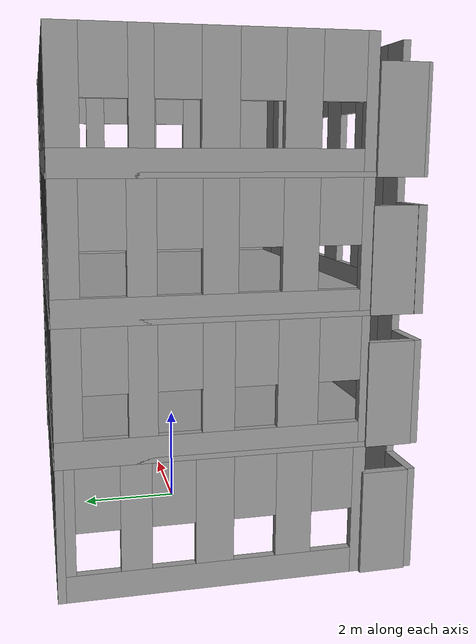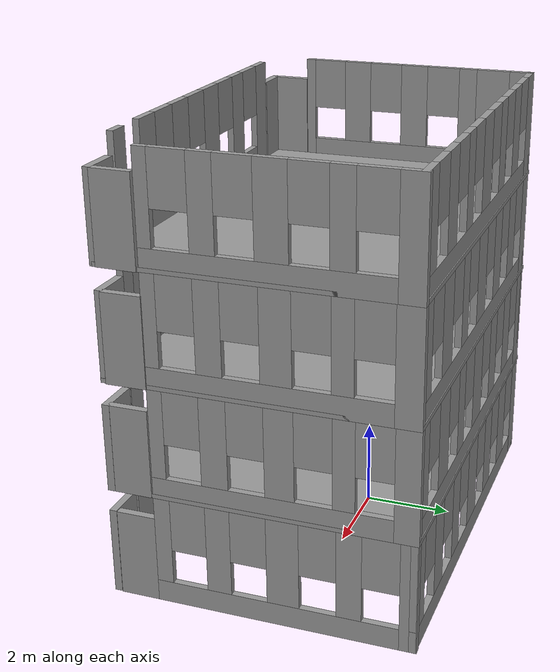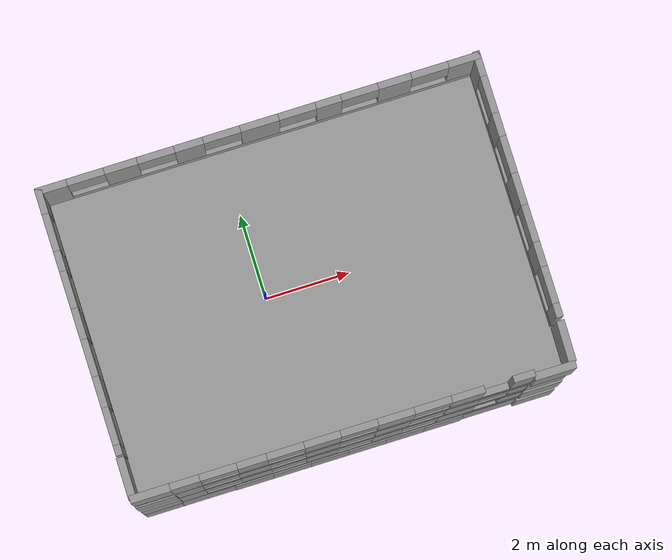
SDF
<?xml version='1.0'?>
<sdf version='1.7'>
  <model name='domitory'>
    <pose>0.765108 -0.598707 0 0 -0 0</pose>
    <link name='Door_0'>
      <collision name='Door_0_Collision'>
        <geometry>
          <box>
            <size>0.9 0.17 2</size>
          </box>
        </geometry>
        <pose>0 0 1 0 -0 0</pose>
      </collision>
      <visual name='Door_0_Visual'>
        <pose>0 0 1 0 -0 0</pose>
        <geometry>
          <box>
            <size>0.9 0.17 2</size>
          </box>
        </geometry>
        <material>
          <script>
            <uri>file://media/materials/scripts/gazebo.material</uri>
            <name>Gazebo/Grey</name>
          </script>
        </material>
      </visual>
      <pose>-2.25511 -3.31129 0 0 -0 0</pose>
    </link>
    <link name='Door_1'>
      <collision name='Door_1_Collision'>
        <geometry>
          <box>
            <size>0.9 0.17 2</size>
          </box>
        </geometry>
        <pose>0 0 1 0 -0 0</pose>
      </collision>
      <visual name='Door_1_Visual'>
        <pose>0 0 1 0 -0 0</pose>
        <geometry>
          <box>
            <size>0.9 0.17 2</size>
          </box>
        </geometry>
        <material>
          <script>
            <uri>file://media/materials/scripts/gazebo.material</uri>
            <name>Gazebo/Grey</name>
          </script>
        </material>
      </visual>
      <pose>-1.36511 -3.31129 0 0 -0 0</pose>
    </link>
    <link name='Door_10'>
      <collision name='Door_10_Collision'>
        <geometry>
          <box>
            <size>0.9 0.17 2</size>
          </box>
        </geometry>
        <pose>0 0 1 0 -0 0</pose>
      </collision>
      <visual name='Door_10_Visual'>
        <pose>0 0 1 0 -0 0</pose>
        <geometry>
          <box>
            <size>0.9 0.17 2</size>
          </box>
        </geometry>
        <material>
          <script>
            <uri>file://media/materials/scripts/gazebo.material</uri>
            <name>Gazebo/Grey</name>
          </script>
        </material>
      </visual>
      <pose>-4.35997 -3.32416 2.5 0 -0 0</pose>
    </link>
    <link name='Door_11'>
      <collision name='Door_11_Collision'>
        <geometry>
          <box>
            <size>0.9 0.17 2</size>
          </box>
        </geometry>
        <pose>0 0 1 0 -0 0</pose>
      </collision>
      <visual name='Door_11_Visual'>
        <pose>0 0 1 0 -0 0</pose>
        <geometry>
          <box>
            <size>0.9 0.17 2</size>
          </box>
        </geometry>
        <material>
          <script>
            <uri>file://media/materials/scripts/gazebo.material</uri>
            <name>Gazebo/Grey</name>
          </script>
        </material>
      </visual>
      <pose>-4.75143 -2.81388 2.5 0 0 -1.56498</pose>
    </link>
    <link name='Door_12'>
      <collision name='Door_12_Collision'>
        <geometry>
          <box>
            <size>0.9 0.17 2</size>
          </box>
        </geometry>
        <pose>0 0 1 0 -0 0</pose>
      </collision>
      <visual name='Door_12_Visual'>
        <pose>0 0 1 0 -0 0</pose>
        <geometry>
          <box>
            <size>0.9 0.17 2</size>
          </box>
        </geometry>
        <material>
          <script>
            <uri>file://media/materials/scripts/gazebo.material</uri>
            <name>Gazebo/Grey</name>
          </script>
        </material>
      </visual>
      <pose>4.35367 -3.32593 2.5 0 -0 0</pose>
    </link>
    <link name='Door_13'>
      <collision name='Door_13_Collision'>
        <geometry>
          <box>
            <size>0.9 0.17 2</size>
          </box>
        </geometry>
        <pose>0 0 1 0 -0 0</pose>
      </collision>
      <visual name='Door_13_Visual'>
        <pose>0 0 1 0 -0 0</pose>
        <geometry>
          <box>
            <size>0.9 0.17 2</size>
          </box>
        </geometry>
        <material>
          <script>
            <uri>file://media/materials/scripts/gazebo.material</uri>
            <name>Gazebo/Grey</name>
          </script>
        </material>
      </visual>
      <pose>4.71868 -2.83925 2.5 0 -0 1.56606</pose>
    </link>
    <link name='Door_14'>
      <collision name='Door_14_Collision'>
        <geometry>
          <box>
            <size>0.9 0.17 2</size>
          </box>
        </geometry>
        <pose>0 0 1 0 -0 0</pose>
      </collision>
      <visual name='Door_14_Visual'>
        <pose>0 0 1 0 -0 0</pose>
        <geometry>
          <box>
            <size>0.9 0.17 2</size>
          </box>
        </geometry>
        <material>
          <script>
            <uri>file://media/materials/scripts/gazebo.material</uri>
            <name>Gazebo/Grey</name>
          </script>
        </material>
      </visual>
      <pose>-4.372 -3.31425 5 0 -0 0</pose>
    </link>
    <link name='Door_15'>
      <collision name='Door_15_Collision'>
        <geometry>
          <box>
            <size>0.9 0.17 2</size>
          </box>
        </geometry>
        <pose>0 0 1 0 -0 0</pose>
      </collision>
      <visual name='Door_15_Visual'>
        <pose>0 0 1 0 -0 0</pose>
        <geometry>
          <box>
            <size>0.9 0.17 2</size>
          </box>
        </geometry>
        <material>
          <script>
            <uri>file://media/materials/scripts/gazebo.material</uri>
            <name>Gazebo/Grey</name>
          </script>
        </material>
      </visual>
      <pose>-4.73404 -2.82147 5 0 0 -1.55925</pose>
    </link>
    <link name='Door_16'>
      <collision name='Door_16_Collision'>
        <geometry>
          <box>
            <size>0.9 0.17 2</size>
          </box>
        </geometry>
        <pose>0 0 1 0 -0 0</pose>
      </collision>
      <visual name='Door_16_Visual'>
        <pose>0 0 1 0 -0 0</pose>
        <geometry>
          <box>
            <size>0.9 0.17 2</size>
          </box>
        </geometry>
        <material>
          <script>
            <uri>file://media/materials/scripts/gazebo.material</uri>
            <name>Gazebo/Grey</name>
          </script>
        </material>
      </visual>
      <pose>4.33718 -3.3042 5 0 -0 0</pose>
    </link>
    <link name='Door_17'>
      <collision name='Door_17_Collision'>
        <geometry>
          <box>
            <size>0.9 0.17 2</size>
          </box>
        </geometry>
        <pose>0 0 1 0 -0 0</pose>
      </collision>
      <visual name='Door_17_Visual'>
        <pose>0 0 1 0 -0 0</pose>
        <geometry>
          <box>
            <size>0.9 0.17 2</size>
          </box>
        </geometry>
        <material>
          <script>
            <uri>file://media/materials/scripts/gazebo.material</uri>
            <name>Gazebo/Grey</name>
          </script>
        </material>
      </visual>
      <pose>4.74951 -2.80136 5 0 -0 1.58063</pose>
    </link>
    <link name='Door_18'>
      <collision name='Door_18_Collision'>
        <geometry>
          <box>
            <size>0.9 0.17 2</size>
          </box>
        </geometry>
        <pose>0 0 1 0 -0 0</pose>
      </collision>
      <visual name='Door_18_Visual'>
        <pose>0 0 1 0 -0 0</pose>
        <geometry>
          <box>
            <size>0.9 0.17 2</size>
          </box>
        </geometry>
        <material>
          <script>
            <uri>file://media/materials/scripts/gazebo.material</uri>
            <name>Gazebo/Grey</name>
          </script>
        </material>
      </visual>
      <pose>-4.36107 -3.29465 7.5 0 -0 0</pose>
    </link>
    <link name='Door_19'>
      <collision name='Door_19_Collision'>
        <geometry>
          <box>
            <size>0.9 0.17 2</size>
          </box>
        </geometry>
        <pose>0 0 1 0 -0 0</pose>
      </collision>
      <visual name='Door_19_Visual'>
        <pose>0 0 1 0 -0 0</pose>
        <geometry>
          <box>
            <size>0.9 0.17 2</size>
          </box>
        </geometry>
        <material>
          <script>
            <uri>file://media/materials/scripts/gazebo.material</uri>
            <name>Gazebo/Grey</name>
          </script>
        </material>
      </visual>
      <pose>-4.7454 -2.84964 7.5 0 -0 -1.5754</pose>
    </link>
    <link name='Door_2'>
      <collision name='Door_2_Collision'>
        <geometry>
          <box>
            <size>0.9 0.17 2</size>
          </box>
        </geometry>
        <pose>0 0 1 0 -0 0</pose>
      </collision>
      <visual name='Door_2_Visual'>
        <pose>0 0 1 0 -0 0</pose>
        <geometry>
          <box>
            <size>0.9 0.17 2</size>
          </box>
        </geometry>
        <material>
          <script>
            <uri>file://media/materials/scripts/gazebo.material</uri>
            <name>Gazebo/Grey</name>
          </script>
        </material>
      </visual>
      <pose>-0.475108 -3.31129 0 0 -0 0</pose>
    </link>
    <link name='Door_20'>
      <collision name='Door_20_Collision'>
        <geometry>
          <box>
            <size>0.9 0.17 2</size>
          </box>
        </geometry>
        <pose>0 0 1 0 -0 0</pose>
      </collision>
      <visual name='Door_20_Visual'>
        <pose>0 0 1 0 -0 0</pose>
        <geometry>
          <box>
            <size>0.9 0.17 2</size>
          </box>
        </geometry>
        <material>
          <script>
            <uri>file://media/materials/scripts/gazebo.material</uri>
            <name>Gazebo/Grey</name>
          </script>
        </material>
      </visual>
      <pose>4.33688 -3.35533 7.5 0 -0 0</pose>
    </link>
    <link name='Door_21'>
      <collision name='Door_21_Collision'>
        <geometry>
          <box>
            <size>0.9 0.17 2</size>
          </box>
        </geometry>
        <pose>0 0 1 0 -0 0</pose>
      </collision>
      <visual name='Door_21_Visual'>
        <pose>0 0 1 0 -0 0</pose>
        <geometry>
          <box>
            <size>0.9 0.17 2</size>
          </box>
        </geometry>
        <material>
          <script>
            <uri>file://media/materials/scripts/gazebo.material</uri>
            <name>Gazebo/Grey</name>
          </script>
        </material>
      </visual>
      <pose>4.74144 -2.84964 7.5 0 -0 1.55325</pose>
    </link>
    <link name='Door_3'>
      <collision name='Door_3_Collision'>
        <geometry>
          <box>
            <size>0.9 0.17 2</size>
          </box>
        </geometry>
        <pose>0 0 1 0 -0 0</pose>
      </collision>
      <visual name='Door_3_Visual'>
        <pose>0 0 1 0 -0 0</pose>
        <geometry>
          <box>
            <size>0.9 0.17 2</size>
          </box>
        </geometry>
        <material>
          <script>
            <uri>file://media/materials/scripts/gazebo.material</uri>
            <name>Gazebo/Grey</name>
          </script>
        </material>
      </visual>
      <pose>0.414892 -3.31129 0 0 -0 0</pose>
    </link>
    <link name='Door_4'>
      <collision name='Door_4_Collision'>
        <geometry>
          <box>
            <size>0.9 0.17 2</size>
          </box>
        </geometry>
        <pose>0 0 1 0 -0 0</pose>
      </collision>
      <visual name='Door_4_Visual'>
        <pose>0 0 1 0 -0 0</pose>
        <geometry>
          <box>
            <size>0.9 0.17 2</size>
          </box>
        </geometry>
        <material>
          <script>
            <uri>file://media/materials/scripts/gazebo.material</uri>
            <name>Gazebo/Grey</name>
          </script>
        </material>
      </visual>
      <pose>1.30489 -3.31129 0 0 -0 0</pose>
    </link>
    <link name='Door_5'>
      <collision name='Door_5_Collision'>
        <geometry>
          <box>
            <size>0.9 0.17 2</size>
          </box>
        </geometry>
        <pose>0 0 1 0 -0 0</pose>
      </collision>
      <visual name='Door_5_Visual'>
        <pose>0 0 1 0 -0 0</pose>
        <geometry>
          <box>
            <size>0.9 0.17 2</size>
          </box>
        </geometry>
        <material>
          <script>
            <uri>file://media/materials/scripts/gazebo.material</uri>
            <name>Gazebo/Grey</name>
          </script>
        </material>
      </visual>
      <pose>2.20489 -3.31129 0 0 -0 0</pose>
    </link>
    <link name='Door_6'>
      <collision name='Door_6_Collision'>
        <geometry>
          <box>
            <size>0.9 0.17 2</size>
          </box>
        </geometry>
        <pose>0 0 1 0 -0 0</pose>
      </collision>
      <visual name='Door_6_Visual'>
        <pose>0 0 1 0 -0 0</pose>
        <geometry>
          <box>
            <size>0.9 0.17 2</size>
          </box>
        </geometry>
        <material>
          <script>
            <uri>file://media/materials/scripts/gazebo.material</uri>
            <name>Gazebo/Grey</name>
          </script>
        </material>
      </visual>
      <pose>-4.37511 -3.30129 0 0 -0 0</pose>
    </link>
    <link name='Door_7'>
      <collision name='Door_7_Collision'>
        <geometry>
          <box>
            <size>0.9 0.17 2</size>
          </box>
        </geometry>
        <pose>0 0 1 0 -0 0</pose>
      </collision>
      <visual name='Door_7_Visual'>
        <pose>0 0 1 0 -0 0</pose>
        <geometry>
          <box>
            <size>0.9 0.17 2</size>
          </box>
        </geometry>
        <material>
          <script>
            <uri>file://media/materials/scripts/gazebo.material</uri>
            <name>Gazebo/Grey</name>
          </script>
        </material>
      </visual>
      <pose>-4.79009 -2.77129 0 0 0 -1.56404</pose>
    </link>
    <link name='Door_8'>
      <collision name='Door_8_Collision'>
        <geometry>
          <box>
            <size>0.9 0.17 2</size>
          </box>
        </geometry>
        <pose>0 0 1 0 -0 0</pose>
      </collision>
      <visual name='Door_8_Visual'>
        <pose>0 0 1 0 -0 0</pose>
        <geometry>
          <box>
            <size>0.9 0.17 2</size>
          </box>
        </geometry>
        <material>
          <script>
            <uri>file://media/materials/scripts/gazebo.material</uri>
            <name>Gazebo/Grey</name>
          </script>
        </material>
      </visual>
      <pose>4.33084 -3.34889 0 0 -0 0</pose>
    </link>
    <link name='Door_9'>
      <collision name='Door_9_Collision'>
        <geometry>
          <box>
            <size>0.9 0.17 2</size>
          </box>
        </geometry>
        <pose>0 0 1 0 -0 0</pose>
      </collision>
      <visual name='Door_9_Visual'>
        <pose>0 0 1 0 -0 0</pose>
        <geometry>
          <box>
            <size>0.9 0.17 2</size>
          </box>
        </geometry>
        <material>
          <script>
            <uri>file://media/materials/scripts/gazebo.material</uri>
            <name>Gazebo/Grey</name>
          </script>
        </material>
      </visual>
      <pose>4.71207 -2.79987 0 0 -0 1.57105</pose>
    </link>
    <link name='Floor_0'>
      <collision name='Floor_0_Collision'>
        <geometry>
          <box>
            <size>9.59773 6.77259 0.1</size>
          </box>
        </geometry>
        <pose>0 0 0.05 0 -0 0</pose>
      </collision>
      <visual name='Floor_0_Visual'>
        <pose>0 0 0.05 0 -0 0</pose>
        <geometry>
          <box>
            <size>9.59773 6.77259 0.1</size>
          </box>
        </geometry>
        <material>
          <script>
            <uri>file://media/materials/scripts/gazebo.material</uri>
            <name>Gazebo/Grey</name>
          </script>
          <ambient>1 1 1 1</ambient>
        </material>
        <meta>
          <layer>1</layer>
        </meta>
      </visual>
      <pose>-0 -0 2.5 0 -0 0</pose>
    </link>
    <link name='Floor_1'>
      <collision name='Floor_1_Collision'>
        <geometry>
          <box>
            <size>9.59773 6.77259 0.1</size>
          </box>
        </geometry>
        <pose>0 0 0.05 0 -0 0</pose>
      </collision>
      <visual name='Floor_1_Visual'>
        <pose>0 0 0.05 0 -0 0</pose>
        <geometry>
          <box>
            <size>9.59773 6.77259 0.1</size>
          </box>
        </geometry>
        <material>
          <script>
            <uri>file://media/materials/scripts/gazebo.material</uri>
            <name>Gazebo/Grey</name>
          </script>
          <ambient>1 1 1 1</ambient>
        </material>
        <meta>
          <layer>2</layer>
        </meta>
      </visual>
      <pose>-0 -0 5 0 -0 0</pose>
    </link>
    <link name='Floor_2'>
      <collision name='Floor_2_Collision'>
        <geometry>
          <box>
            <size>9.59773 6.77259 0.1</size>
          </box>
        </geometry>
        <pose>0 0 0.05 0 -0 0</pose>
      </collision>
      <visual name='Floor_2_Visual'>
        <pose>0 0 0.05 0 -0 0</pose>
        <geometry>
          <box>
            <size>9.59773 6.77259 0.1</size>
          </box>
        </geometry>
        <material>
          <script>
            <uri>file://media/materials/scripts/gazebo.material</uri>
            <name>Gazebo/Grey</name>
          </script>
          <ambient>1 1 1 1</ambient>
        </material>
        <meta>
          <layer>3</layer>
        </meta>
      </visual>
      <pose>-0 -0 7.5 0 -0 0</pose>
    </link>
    <link name='Wall_0'>
      <collision name='Wall_0_Collision'>
        <geometry>
          <box>
            <size>1.25 0.15 2.5</size>
          </box>
        </geometry>
        <pose>0 0 1.25 0 -0 0</pose>
      </collision>
      <visual name='Wall_0_Visual'>
        <pose>0 0 1.25 0 -0 0</pose>
        <geometry>
          <box>
            <size>1.25 0.15 2.5</size>
          </box>
        </geometry>
        <material>
          <script>
            <uri>file://media/materials/scripts/gazebo.material</uri>
            <name>Gazebo/Grey</name>
          </script>
          <ambient>1 1 1 1</ambient>
        </material>
        <meta>
          <layer>0</layer>
        </meta>
      </visual>
      <pose>-3.31511 -3.31129 0 0 -0 0</pose>
    </link>
    <link name='Wall_10'>
      <pose>-4.72386 0.491179 2.5 0 -0 1.5708</pose>
      <visual name='Wall_10_Visual_0'>
        <pose>-2.79234 0 1.25 0 -0 0</pose>
        <geometry>
          <box>
            <size>0.165329 0.15 2.5</size>
          </box>
        </geometry>
        <material>
          <script>
            <uri>file://media/materials/scripts/gazebo.material</uri>
            <name>Gazebo/Grey</name>
          </script>
          <ambient>1 1 1 1</ambient>
        </material>
        <meta>
          <layer>1</layer>
        </meta>
      </visual>
      <collision name='Wall_10_Collision_0'>
        <geometry>
          <box>
            <size>0.165329 0.15 2.5</size>
          </box>
        </geometry>
        <pose>-2.79234 0 1.25 0 -0 0</pose>
      </collision>
      <visual name='Wall_10_Visual_1'>
        <pose>0.082664 0 0.25 0 -0 0</pose>
        <geometry>
          <box>
            <size>5.58467 0.15 0.5</size>
          </box>
        </geometry>
        <material>
          <script>
            <uri>file://media/materials/scripts/gazebo.material</uri>
            <name>Gazebo/Grey</name>
          </script>
          <ambient>1 1 1 1</ambient>
        </material>
        <meta>
          <layer>1</layer>
        </meta>
      </visual>
      <collision name='Wall_10_Collision_1'>
        <geometry>
          <box>
            <size>5.58467 0.15 0.5</size>
          </box>
        </geometry>
        <pose>0.082664 0 0.25 0 -0 0</pose>
      </collision>
      <visual name='Wall_10_Visual_2'>
        <pose>-1.52323 0 1.5 0 -0 0</pose>
        <geometry>
          <box>
            <size>0.772881 0.15 2</size>
          </box>
        </geometry>
        <material>
          <script>
            <uri>file://media/materials/scripts/gazebo.material</uri>
            <name>Gazebo/Grey</name>
          </script>
          <ambient>1 1 1 1</ambient>
        </material>
        <meta>
          <layer>1</layer>
        </meta>
      </visual>
      <collision name='Wall_10_Collision_2'>
        <geometry>
          <box>
            <size>0.772881 0.15 2</size>
          </box>
        </geometry>
        <pose>-1.52323 0 1.5 0 -0 0</pose>
      </collision>
      <visual name='Wall_10_Visual_3'>
        <pose>-0.042872 0 1.5 0 -0 0</pose>
        <geometry>
          <box>
            <size>0.587836 0.15 2</size>
          </box>
        </geometry>
        <material>
          <script>
            <uri>file://media/materials/scripts/gazebo.material</uri>
            <name>Gazebo/Grey</name>
          </script>
          <ambient>1 1 1 1</ambient>
        </material>
        <meta>
          <layer>1</layer>
        </meta>
      </visual>
      <collision name='Wall_10_Collision_3'>
        <geometry>
          <box>
            <size>0.587836 0.15 2</size>
          </box>
        </geometry>
        <pose>-0.042872 0 1.5 0 -0 0</pose>
      </collision>
      <visual name='Wall_10_Visual_4'>
        <pose>1.31027 0 1.5 0 -0 0</pose>
        <geometry>
          <box>
            <size>0.518445 0.15 2</size>
          </box>
        </geometry>
        <material>
          <script>
            <uri>file://media/materials/scripts/gazebo.material</uri>
            <name>Gazebo/Grey</name>
          </script>
          <ambient>1 1 1 1</ambient>
        </material>
        <meta>
          <layer>1</layer>
        </meta>
      </visual>
      <collision name='Wall_10_Collision_4'>
        <geometry>
          <box>
            <size>0.518445 0.15 2</size>
          </box>
        </geometry>
        <pose>1.31027 0 1.5 0 -0 0</pose>
      </collision>
      <visual name='Wall_10_Visual_5'>
        <pose>2.62225 0 1.5 0 -0 0</pose>
        <geometry>
          <box>
            <size>0.505509 0.15 2</size>
          </box>
        </geometry>
        <material>
          <script>
            <uri>file://media/materials/scripts/gazebo.material</uri>
            <name>Gazebo/Grey</name>
          </script>
          <ambient>1 1 1 1</ambient>
        </material>
        <meta>
          <layer>1</layer>
        </meta>
      </visual>
      <collision name='Wall_10_Collision_5'>
        <geometry>
          <box>
            <size>0.505509 0.15 2</size>
          </box>
        </geometry>
        <pose>2.62225 0 1.5 0 -0 0</pose>
      </collision>
      <visual name='Wall_10_Visual_6'>
        <pose>-2.30967 0 1.9 0 -0 0</pose>
        <geometry>
          <box>
            <size>0.8 0.15 1.2</size>
          </box>
        </geometry>
        <material>
          <script>
            <uri>file://media/materials/scripts/gazebo.material</uri>
            <name>Gazebo/Grey</name>
          </script>
          <ambient>1 1 1 1</ambient>
        </material>
        <meta>
          <layer>1</layer>
        </meta>
      </visual>
      <collision name='Wall_10_Collision_6'>
        <geometry>
          <box>
            <size>0.8 0.15 1.2</size>
          </box>
        </geometry>
        <pose>-2.30967 0 1.9 0 -0 0</pose>
      </collision>
      <visual name='Wall_10_Visual_7'>
        <pose>-0.73679 0 1.9 0 -0 0</pose>
        <geometry>
          <box>
            <size>0.8 0.15 1.2</size>
          </box>
        </geometry>
        <material>
          <script>
            <uri>file://media/materials/scripts/gazebo.material</uri>
            <name>Gazebo/Grey</name>
          </script>
          <ambient>1 1 1 1</ambient>
        </material>
        <meta>
          <layer>1</layer>
        </meta>
      </visual>
      <collision name='Wall_10_Collision_7'>
        <geometry>
          <box>
            <size>0.8 0.15 1.2</size>
          </box>
        </geometry>
        <pose>-0.73679 0 1.9 0 -0 0</pose>
      </collision>
      <visual name='Wall_10_Visual_8'>
        <pose>0.651047 0 1.9 0 -0 0</pose>
        <geometry>
          <box>
            <size>0.8 0.15 1.2</size>
          </box>
        </geometry>
        <material>
          <script>
            <uri>file://media/materials/scripts/gazebo.material</uri>
            <name>Gazebo/Grey</name>
          </script>
          <ambient>1 1 1 1</ambient>
        </material>
        <meta>
          <layer>1</layer>
        </meta>
      </visual>
      <collision name='Wall_10_Collision_8'>
        <geometry>
          <box>
            <size>0.8 0.15 1.2</size>
          </box>
        </geometry>
        <pose>0.651047 0 1.9 0 -0 0</pose>
      </collision>
      <visual name='Wall_10_Visual_9'>
        <pose>1.96949 0 1.9 0 -0 0</pose>
        <geometry>
          <box>
            <size>0.8 0.15 1.2</size>
          </box>
        </geometry>
        <material>
          <script>
            <uri>file://media/materials/scripts/gazebo.material</uri>
            <name>Gazebo/Grey</name>
          </script>
          <ambient>1 1 1 1</ambient>
        </material>
        <meta>
          <layer>1</layer>
        </meta>
      </visual>
      <collision name='Wall_10_Collision_9'>
        <geometry>
          <box>
            <size>0.8 0.15 1.2</size>
          </box>
        </geometry>
        <pose>1.96949 0 1.9 0 -0 0</pose>
      </collision>
    </link>
    <link name='Wall_11'>
      <pose>-0 3.29118 2.5 0 -0 0</pose>
      <visual name='Wall_11_Visual_0'>
        <pose>-4.4928 0 1.25 0 -0 0</pose>
        <geometry>
          <box>
            <size>0.612127 0.15 2.5</size>
          </box>
        </geometry>
        <material>
          <script>
            <uri>file://media/materials/scripts/gazebo.material</uri>
            <name>Gazebo/Grey</name>
          </script>
          <ambient>1 1 1 1</ambient>
        </material>
        <meta>
          <layer>1</layer>
        </meta>
      </visual>
      <collision name='Wall_11_Collision_0'>
        <geometry>
          <box>
            <size>0.612127 0.15 2.5</size>
          </box>
        </geometry>
        <pose>-4.4928 0 1.25 0 -0 0</pose>
      </collision>
      <visual name='Wall_11_Visual_1'>
        <pose>0.306063 0 0.25 0 -0 0</pose>
        <geometry>
          <box>
            <size>8.9856 0.15 0.5</size>
          </box>
        </geometry>
        <material>
          <script>
            <uri>file://media/materials/scripts/gazebo.material</uri>
            <name>Gazebo/Grey</name>
          </script>
          <ambient>1 1 1 1</ambient>
        </material>
        <meta>
          <layer>1</layer>
        </meta>
      </visual>
      <collision name='Wall_11_Collision_1'>
        <geometry>
          <box>
            <size>8.9856 0.15 0.5</size>
          </box>
        </geometry>
        <pose>0.306063 0 0.25 0 -0 0</pose>
      </collision>
      <visual name='Wall_11_Visual_2'>
        <pose>-3.02592 0 1.5 0 -0 0</pose>
        <geometry>
          <box>
            <size>0.721636 0.15 2</size>
          </box>
        </geometry>
        <material>
          <script>
            <uri>file://media/materials/scripts/gazebo.material</uri>
            <name>Gazebo/Grey</name>
          </script>
          <ambient>1 1 1 1</ambient>
        </material>
        <meta>
          <layer>1</layer>
        </meta>
      </visual>
      <collision name='Wall_11_Collision_2'>
        <geometry>
          <box>
            <size>0.721636 0.15 2</size>
          </box>
        </geometry>
        <pose>-3.02592 0 1.5 0 -0 0</pose>
      </collision>
      <visual name='Wall_11_Visual_3'>
        <pose>-1.53052 0 1.5 0 -0 0</pose>
        <geometry>
          <box>
            <size>0.669165 0.15 2</size>
          </box>
        </geometry>
        <material>
          <script>
            <uri>file://media/materials/scripts/gazebo.material</uri>
            <name>Gazebo/Grey</name>
          </script>
          <ambient>1 1 1 1</ambient>
        </material>
        <meta>
          <layer>1</layer>
        </meta>
      </visual>
      <collision name='Wall_11_Collision_3'>
        <geometry>
          <box>
            <size>0.669165 0.15 2</size>
          </box>
        </geometry>
        <pose>-1.53052 0 1.5 0 -0 0</pose>
      </collision>
      <visual name='Wall_11_Visual_4'>
        <pose>0.017351 0 1.5 0 -0 0</pose>
        <geometry>
          <box>
            <size>0.826576 0.15 2</size>
          </box>
        </geometry>
        <material>
          <script>
            <uri>file://media/materials/scripts/gazebo.material</uri>
            <name>Gazebo/Grey</name>
          </script>
          <ambient>1 1 1 1</ambient>
        </material>
        <meta>
          <layer>1</layer>
        </meta>
      </visual>
      <collision name='Wall_11_Collision_4'>
        <geometry>
          <box>
            <size>0.826576 0.15 2</size>
          </box>
        </geometry>
        <pose>0.017351 0 1.5 0 -0 0</pose>
      </collision>
      <visual name='Wall_11_Visual_5'>
        <pose>1.51275 0 1.5 0 -0 0</pose>
        <geometry>
          <box>
            <size>0.564225 0.15 2</size>
          </box>
        </geometry>
        <material>
          <script>
            <uri>file://media/materials/scripts/gazebo.material</uri>
            <name>Gazebo/Grey</name>
          </script>
          <ambient>1 1 1 1</ambient>
        </material>
        <meta>
          <layer>1</layer>
        </meta>
      </visual>
      <collision name='Wall_11_Collision_5'>
        <geometry>
          <box>
            <size>0.564225 0.15 2</size>
          </box>
        </geometry>
        <pose>1.51275 0 1.5 0 -0 0</pose>
      </collision>
      <visual name='Wall_11_Visual_6'>
        <pose>2.99066 0 1.5 0 -0 0</pose>
        <geometry>
          <box>
            <size>0.791596 0.15 2</size>
          </box>
        </geometry>
        <material>
          <script>
            <uri>file://media/materials/scripts/gazebo.material</uri>
            <name>Gazebo/Grey</name>
          </script>
          <ambient>1 1 1 1</ambient>
        </material>
        <meta>
          <layer>1</layer>
        </meta>
      </visual>
      <collision name='Wall_11_Collision_6'>
        <geometry>
          <box>
            <size>0.791596 0.15 2</size>
          </box>
        </geometry>
        <pose>2.99066 0 1.5 0 -0 0</pose>
      </collision>
      <visual name='Wall_11_Visual_7'>
        <pose>4.49266 0 1.5 0 -0 0</pose>
        <geometry>
          <box>
            <size>0.612404 0.15 2</size>
          </box>
        </geometry>
        <material>
          <script>
            <uri>file://media/materials/scripts/gazebo.material</uri>
            <name>Gazebo/Grey</name>
          </script>
          <ambient>1 1 1 1</ambient>
        </material>
        <meta>
          <layer>1</layer>
        </meta>
      </visual>
      <collision name='Wall_11_Collision_7'>
        <geometry>
          <box>
            <size>0.612404 0.15 2</size>
          </box>
        </geometry>
        <pose>4.49266 0 1.5 0 -0 0</pose>
      </collision>
      <visual name='Wall_11_Visual_8'>
        <pose>-3.78674 0 1.9 0 -0 0</pose>
        <geometry>
          <box>
            <size>0.8 0.15 1.2</size>
          </box>
        </geometry>
        <material>
          <script>
            <uri>file://media/materials/scripts/gazebo.material</uri>
            <name>Gazebo/Grey</name>
          </script>
          <ambient>1 1 1 1</ambient>
        </material>
        <meta>
          <layer>1</layer>
        </meta>
      </visual>
      <collision name='Wall_11_Collision_8'>
        <geometry>
          <box>
            <size>0.8 0.15 1.2</size>
          </box>
        </geometry>
        <pose>-3.78674 0 1.9 0 -0 0</pose>
      </collision>
      <visual name='Wall_11_Visual_9'>
        <pose>-2.2651 0 1.9 0 -0 0</pose>
        <geometry>
          <box>
            <size>0.8 0.15 1.2</size>
          </box>
        </geometry>
        <material>
          <script>
            <uri>file://media/materials/scripts/gazebo.material</uri>
            <name>Gazebo/Grey</name>
          </script>
          <ambient>1 1 1 1</ambient>
        </material>
        <meta>
          <layer>1</layer>
        </meta>
      </visual>
      <collision name='Wall_11_Collision_9'>
        <geometry>
          <box>
            <size>0.8 0.15 1.2</size>
          </box>
        </geometry>
        <pose>-2.2651 0 1.9 0 -0 0</pose>
      </collision>
      <visual name='Wall_11_Visual_10'>
        <pose>-0.795937 0 1.9 0 -0 0</pose>
        <geometry>
          <box>
            <size>0.8 0.15 1.2</size>
          </box>
        </geometry>
        <material>
          <script>
            <uri>file://media/materials/scripts/gazebo.material</uri>
            <name>Gazebo/Grey</name>
          </script>
          <ambient>1 1 1 1</ambient>
        </material>
        <meta>
          <layer>1</layer>
        </meta>
      </visual>
      <collision name='Wall_11_Collision_10'>
        <geometry>
          <box>
            <size>0.8 0.15 1.2</size>
          </box>
        </geometry>
        <pose>-0.795937 0 1.9 0 -0 0</pose>
      </collision>
      <visual name='Wall_11_Visual_11'>
        <pose>0.830639 0 1.9 0 -0 0</pose>
        <geometry>
          <box>
            <size>0.8 0.15 1.2</size>
          </box>
        </geometry>
        <material>
          <script>
            <uri>file://media/materials/scripts/gazebo.material</uri>
            <name>Gazebo/Grey</name>
          </script>
          <ambient>1 1 1 1</ambient>
        </material>
        <meta>
          <layer>1</layer>
        </meta>
      </visual>
      <collision name='Wall_11_Collision_11'>
        <geometry>
          <box>
            <size>0.8 0.15 1.2</size>
          </box>
        </geometry>
        <pose>0.830639 0 1.9 0 -0 0</pose>
      </collision>
      <visual name='Wall_11_Visual_12'>
        <pose>2.19486 0 1.9 0 -0 0</pose>
        <geometry>
          <box>
            <size>0.8 0.15 1.2</size>
          </box>
        </geometry>
        <material>
          <script>
            <uri>file://media/materials/scripts/gazebo.material</uri>
            <name>Gazebo/Grey</name>
          </script>
          <ambient>1 1 1 1</ambient>
        </material>
        <meta>
          <layer>1</layer>
        </meta>
      </visual>
      <collision name='Wall_11_Collision_12'>
        <geometry>
          <box>
            <size>0.8 0.15 1.2</size>
          </box>
        </geometry>
        <pose>2.19486 0 1.9 0 -0 0</pose>
      </collision>
      <visual name='Wall_11_Visual_13'>
        <pose>3.78646 0 1.9 0 -0 0</pose>
        <geometry>
          <box>
            <size>0.8 0.15 1.2</size>
          </box>
        </geometry>
        <material>
          <script>
            <uri>file://media/materials/scripts/gazebo.material</uri>
            <name>Gazebo/Grey</name>
          </script>
          <ambient>1 1 1 1</ambient>
        </material>
        <meta>
          <layer>1</layer>
        </meta>
      </visual>
      <collision name='Wall_11_Collision_13'>
        <geometry>
          <box>
            <size>0.8 0.15 1.2</size>
          </box>
        </geometry>
        <pose>3.78646 0 1.9 0 -0 0</pose>
      </collision>
    </link>
    <link name='Wall_12'>
      <pose>4.72386 0.511293 2.5 0 -0 -1.5708</pose>
      <visual name='Wall_12_Visual_0'>
        <pose>-2.61219 0 1.25 0 -0 0</pose>
        <geometry>
          <box>
            <size>0.525622 0.15 2.5</size>
          </box>
        </geometry>
        <material>
          <script>
            <uri>file://media/materials/scripts/gazebo.material</uri>
            <name>Gazebo/Grey</name>
          </script>
          <ambient>1 1 1 1</ambient>
        </material>
        <meta>
          <layer>1</layer>
        </meta>
      </visual>
      <collision name='Wall_12_Collision_0'>
        <geometry>
          <box>
            <size>0.525622 0.15 2.5</size>
          </box>
        </geometry>
        <pose>-2.61219 0 1.25 0 -0 0</pose>
      </collision>
      <visual name='Wall_12_Visual_1'>
        <pose>0.262811 0 0.25 0 -0 0</pose>
        <geometry>
          <box>
            <size>5.22438 0.15 0.5</size>
          </box>
        </geometry>
        <material>
          <script>
            <uri>file://media/materials/scripts/gazebo.material</uri>
            <name>Gazebo/Grey</name>
          </script>
          <ambient>1 1 1 1</ambient>
        </material>
        <meta>
          <layer>1</layer>
        </meta>
      </visual>
      <collision name='Wall_12_Collision_1'>
        <geometry>
          <box>
            <size>5.22438 0.15 0.5</size>
          </box>
        </geometry>
        <pose>0.262811 0 0.25 0 -0 0</pose>
      </collision>
      <visual name='Wall_12_Visual_2'>
        <pose>-1.31329 0 1.5 0 -0 0</pose>
        <geometry>
          <box>
            <size>0.472183 0.15 2</size>
          </box>
        </geometry>
        <material>
          <script>
            <uri>file://media/materials/scripts/gazebo.material</uri>
            <name>Gazebo/Grey</name>
          </script>
          <ambient>1 1 1 1</ambient>
        </material>
        <meta>
          <layer>1</layer>
        </meta>
      </visual>
      <collision name='Wall_12_Collision_2'>
        <geometry>
          <box>
            <size>0.472183 0.15 2</size>
          </box>
        </geometry>
        <pose>-1.31329 0 1.5 0 -0 0</pose>
      </collision>
      <visual name='Wall_12_Visual_3'>
        <pose>0.039855 0 1.5 0 -0 0</pose>
        <geometry>
          <box>
            <size>0.634098 0.15 2</size>
          </box>
        </geometry>
        <material>
          <script>
            <uri>file://media/materials/scripts/gazebo.material</uri>
            <name>Gazebo/Grey</name>
          </script>
          <ambient>1 1 1 1</ambient>
        </material>
        <meta>
          <layer>1</layer>
        </meta>
      </visual>
      <collision name='Wall_12_Collision_3'>
        <geometry>
          <box>
            <size>0.634098 0.15 2</size>
          </box>
        </geometry>
        <pose>0.039855 0 1.5 0 -0 0</pose>
      </collision>
      <visual name='Wall_12_Visual_4'>
        <pose>1.45082 0 1.5 0 -0 0</pose>
        <geometry>
          <box>
            <size>0.587836 0.15 2</size>
          </box>
        </geometry>
        <material>
          <script>
            <uri>file://media/materials/scripts/gazebo.material</uri>
            <name>Gazebo/Grey</name>
          </script>
          <ambient>1 1 1 1</ambient>
        </material>
        <meta>
          <layer>1</layer>
        </meta>
      </visual>
      <collision name='Wall_12_Collision_4'>
        <geometry>
          <box>
            <size>0.587836 0.15 2</size>
          </box>
        </geometry>
        <pose>1.45082 0 1.5 0 -0 0</pose>
      </collision>
      <visual name='Wall_12_Visual_5'>
        <pose>2.70987 0 1.5 0 -0 0</pose>
        <geometry>
          <box>
            <size>0.33026 0.15 2</size>
          </box>
        </geometry>
        <material>
          <script>
            <uri>file://media/materials/scripts/gazebo.material</uri>
            <name>Gazebo/Grey</name>
          </script>
          <ambient>1 1 1 1</ambient>
        </material>
        <meta>
          <layer>1</layer>
        </meta>
      </visual>
      <collision name='Wall_12_Collision_5'>
        <geometry>
          <box>
            <size>0.33026 0.15 2</size>
          </box>
        </geometry>
        <pose>2.70987 0 1.5 0 -0 0</pose>
      </collision>
      <visual name='Wall_12_Visual_6'>
        <pose>-1.94938 0 1.9 0 -0 0</pose>
        <geometry>
          <box>
            <size>0.8 0.15 1.2</size>
          </box>
        </geometry>
        <material>
          <script>
            <uri>file://media/materials/scripts/gazebo.material</uri>
            <name>Gazebo/Grey</name>
          </script>
          <ambient>1 1 1 1</ambient>
        </material>
        <meta>
          <layer>1</layer>
        </meta>
      </visual>
      <collision name='Wall_12_Collision_6'>
        <geometry>
          <box>
            <size>0.8 0.15 1.2</size>
          </box>
        </geometry>
        <pose>-1.94938 0 1.9 0 -0 0</pose>
      </collision>
      <visual name='Wall_12_Visual_7'>
        <pose>-0.677194 0 1.9 0 -0 0</pose>
        <geometry>
          <box>
            <size>0.8 0.15 1.2</size>
          </box>
        </geometry>
        <material>
          <script>
            <uri>file://media/materials/scripts/gazebo.material</uri>
            <name>Gazebo/Grey</name>
          </script>
          <ambient>1 1 1 1</ambient>
        </material>
        <meta>
          <layer>1</layer>
        </meta>
      </visual>
      <collision name='Wall_12_Collision_7'>
        <geometry>
          <box>
            <size>0.8 0.15 1.2</size>
          </box>
        </geometry>
        <pose>-0.677194 0 1.9 0 -0 0</pose>
      </collision>
      <visual name='Wall_12_Visual_8'>
        <pose>0.756903 0 1.9 0 -0 0</pose>
        <geometry>
          <box>
            <size>0.8 0.15 1.2</size>
          </box>
        </geometry>
        <material>
          <script>
            <uri>file://media/materials/scripts/gazebo.material</uri>
            <name>Gazebo/Grey</name>
          </script>
          <ambient>1 1 1 1</ambient>
        </material>
        <meta>
          <layer>1</layer>
        </meta>
      </visual>
      <collision name='Wall_12_Collision_8'>
        <geometry>
          <box>
            <size>0.8 0.15 1.2</size>
          </box>
        </geometry>
        <pose>0.756903 0 1.9 0 -0 0</pose>
      </collision>
      <visual name='Wall_12_Visual_9'>
        <pose>2.14474 0 1.9 0 -0 0</pose>
        <geometry>
          <box>
            <size>0.8 0.15 1.2</size>
          </box>
        </geometry>
        <material>
          <script>
            <uri>file://media/materials/scripts/gazebo.material</uri>
            <name>Gazebo/Grey</name>
          </script>
          <ambient>1 1 1 1</ambient>
        </material>
        <meta>
          <layer>1</layer>
        </meta>
      </visual>
      <collision name='Wall_12_Collision_9'>
        <geometry>
          <box>
            <size>0.8 0.15 1.2</size>
          </box>
        </geometry>
        <pose>2.14474 0 1.9 0 -0 0</pose>
      </collision>
    </link>
    <link name='Wall_13'>
      <pose>-0.565108 -3.31129 5 0 -0 0</pose>
      <visual name='Wall_13_Visual_0'>
        <pose>-3.06685 0 1.25 0 -0 0</pose>
        <geometry>
          <box>
            <size>0.616289 0.15 2.5</size>
          </box>
        </geometry>
        <material>
          <script>
            <uri>file://media/materials/scripts/gazebo.material</uri>
            <name>Gazebo/Grey</name>
          </script>
          <ambient>1 1 1 1</ambient>
        </material>
        <meta>
          <layer>2</layer>
        </meta>
      </visual>
      <collision name='Wall_13_Collision_0'>
        <geometry>
          <box>
            <size>0.616289 0.15 2.5</size>
          </box>
        </geometry>
        <pose>-3.06685 0 1.25 0 -0 0</pose>
      </collision>
      <visual name='Wall_13_Visual_1'>
        <pose>0.308145 0 0.25 0 -0 0</pose>
        <geometry>
          <box>
            <size>6.13371 0.15 0.5</size>
          </box>
        </geometry>
        <material>
          <script>
            <uri>file://media/materials/scripts/gazebo.material</uri>
            <name>Gazebo/Grey</name>
          </script>
          <ambient>1 1 1 1</ambient>
        </material>
        <meta>
          <layer>2</layer>
        </meta>
      </visual>
      <collision name='Wall_13_Collision_1'>
        <geometry>
          <box>
            <size>6.13371 0.15 0.5</size>
          </box>
        </geometry>
        <pose>0.308145 0 0.25 0 -0 0</pose>
      </collision>
      <visual name='Wall_13_Visual_2'>
        <pose>-1.61451 0 1.5 0 -0 0</pose>
        <geometry>
          <box>
            <size>0.688404 0.15 2</size>
          </box>
        </geometry>
        <material>
          <script>
            <uri>file://media/materials/scripts/gazebo.material</uri>
            <name>Gazebo/Grey</name>
          </script>
          <ambient>1 1 1 1</ambient>
        </material>
        <meta>
          <layer>2</layer>
        </meta>
      </visual>
      <collision name='Wall_13_Collision_2'>
        <geometry>
          <box>
            <size>0.688404 0.15 2</size>
          </box>
        </geometry>
        <pose>-1.61451 0 1.5 0 -0 0</pose>
      </collision>
      <visual name='Wall_13_Visual_3'>
        <pose>-0.100962 0 1.5 0 -0 0</pose>
        <geometry>
          <box>
            <size>0.738688 0.15 2</size>
          </box>
        </geometry>
        <material>
          <script>
            <uri>file://media/materials/scripts/gazebo.material</uri>
            <name>Gazebo/Grey</name>
          </script>
          <ambient>1 1 1 1</ambient>
        </material>
        <meta>
          <layer>2</layer>
        </meta>
      </visual>
      <collision name='Wall_13_Collision_3'>
        <geometry>
          <box>
            <size>0.738688 0.15 2</size>
          </box>
        </geometry>
        <pose>-0.100962 0 1.5 0 -0 0</pose>
      </collision>
      <visual name='Wall_13_Visual_4'>
        <pose>1.44778 0 1.5 0 -0 0</pose>
        <geometry>
          <box>
            <size>0.758802 0.15 2</size>
          </box>
        </geometry>
        <material>
          <script>
            <uri>file://media/materials/scripts/gazebo.material</uri>
            <name>Gazebo/Grey</name>
          </script>
          <ambient>1 1 1 1</ambient>
        </material>
        <meta>
          <layer>2</layer>
        </meta>
      </visual>
      <collision name='Wall_13_Collision_4'>
        <geometry>
          <box>
            <size>0.758802 0.15 2</size>
          </box>
        </geometry>
        <pose>1.44778 0 1.5 0 -0 0</pose>
      </collision>
      <visual name='Wall_13_Visual_5'>
        <pose>3.00109 0 1.5 0 -0 0</pose>
        <geometry>
          <box>
            <size>0.747816 0.15 2</size>
          </box>
        </geometry>
        <material>
          <script>
            <uri>file://media/materials/scripts/gazebo.material</uri>
            <name>Gazebo/Grey</name>
          </script>
          <ambient>1 1 1 1</ambient>
        </material>
        <meta>
          <layer>2</layer>
        </meta>
      </visual>
      <collision name='Wall_13_Collision_5'>
        <geometry>
          <box>
            <size>0.747816 0.15 2</size>
          </box>
        </geometry>
        <pose>3.00109 0 1.5 0 -0 0</pose>
      </collision>
      <visual name='Wall_13_Visual_6'>
        <pose>-2.35871 0 1.9 0 -0 0</pose>
        <geometry>
          <box>
            <size>0.8 0.15 1.2</size>
          </box>
        </geometry>
        <material>
          <script>
            <uri>file://media/materials/scripts/gazebo.material</uri>
            <name>Gazebo/Grey</name>
          </script>
          <ambient>1 1 1 1</ambient>
        </material>
        <meta>
          <layer>2</layer>
        </meta>
      </visual>
      <collision name='Wall_13_Collision_6'>
        <geometry>
          <box>
            <size>0.8 0.15 1.2</size>
          </box>
        </geometry>
        <pose>-2.35871 0 1.9 0 -0 0</pose>
      </collision>
      <visual name='Wall_13_Visual_7'>
        <pose>-0.870307 0 1.9 0 -0 0</pose>
        <geometry>
          <box>
            <size>0.8 0.15 1.2</size>
          </box>
        </geometry>
        <material>
          <script>
            <uri>file://media/materials/scripts/gazebo.material</uri>
            <name>Gazebo/Grey</name>
          </script>
          <ambient>1 1 1 1</ambient>
        </material>
        <meta>
          <layer>2</layer>
        </meta>
      </visual>
      <collision name='Wall_13_Collision_7'>
        <geometry>
          <box>
            <size>0.8 0.15 1.2</size>
          </box>
        </geometry>
        <pose>-0.870307 0 1.9 0 -0 0</pose>
      </collision>
      <visual name='Wall_13_Visual_8'>
        <pose>0.668382 0 1.9 0 -0 0</pose>
        <geometry>
          <box>
            <size>0.8 0.15 1.2</size>
          </box>
        </geometry>
        <material>
          <script>
            <uri>file://media/materials/scripts/gazebo.material</uri>
            <name>Gazebo/Grey</name>
          </script>
          <ambient>1 1 1 1</ambient>
        </material>
        <meta>
          <layer>2</layer>
        </meta>
      </visual>
      <collision name='Wall_13_Collision_8'>
        <geometry>
          <box>
            <size>0.8 0.15 1.2</size>
          </box>
        </geometry>
        <pose>0.668382 0 1.9 0 -0 0</pose>
      </collision>
      <visual name='Wall_13_Visual_9'>
        <pose>2.22718 0 1.9 0 -0 0</pose>
        <geometry>
          <box>
            <size>0.8 0.15 1.2</size>
          </box>
        </geometry>
        <material>
          <script>
            <uri>file://media/materials/scripts/gazebo.material</uri>
            <name>Gazebo/Grey</name>
          </script>
          <ambient>1 1 1 1</ambient>
        </material>
        <meta>
          <layer>2</layer>
        </meta>
      </visual>
      <collision name='Wall_13_Collision_9'>
        <geometry>
          <box>
            <size>0.8 0.15 1.2</size>
          </box>
        </geometry>
        <pose>2.22718 0 1.9 0 -0 0</pose>
      </collision>
    </link>
    <link name='Wall_14'>
      <pose>3.26489 -3.30129 5 0 -0 0</pose>
      <visual name='Wall_14_Visual_0'>
        <pose>-0.604905 0 1.25 0 -0 0</pose>
        <geometry>
          <box>
            <size>0.04019 0.15 2.5</size>
          </box>
        </geometry>
        <material>
          <script>
            <uri>file://media/materials/scripts/gazebo.material</uri>
            <name>Gazebo/Grey</name>
          </script>
          <ambient>1 1 1 1</ambient>
        </material>
        <meta>
          <layer>2</layer>
        </meta>
      </visual>
      <collision name='Wall_14_Collision_0'>
        <geometry>
          <box>
            <size>0.04019 0.15 2.5</size>
          </box>
        </geometry>
        <pose>-0.604905 0 1.25 0 -0 0</pose>
      </collision>
      <visual name='Wall_14_Visual_1'>
        <pose>0.020095 0 0.25 0 -0 0</pose>
        <geometry>
          <box>
            <size>1.20981 0.15 0.5</size>
          </box>
        </geometry>
        <material>
          <script>
            <uri>file://media/materials/scripts/gazebo.material</uri>
            <name>Gazebo/Grey</name>
          </script>
          <ambient>1 1 1 1</ambient>
        </material>
        <meta>
          <layer>2</layer>
        </meta>
      </visual>
      <collision name='Wall_14_Collision_1'>
        <geometry>
          <box>
            <size>1.20981 0.15 0.5</size>
          </box>
        </geometry>
        <pose>0.020095 0 0.25 0 -0 0</pose>
      </collision>
      <visual name='Wall_14_Visual_2'>
        <pose>0.420095 0 1.5 0 -0 0</pose>
        <geometry>
          <box>
            <size>0.40981 0.15 2</size>
          </box>
        </geometry>
        <material>
          <script>
            <uri>file://media/materials/scripts/gazebo.material</uri>
            <name>Gazebo/Grey</name>
          </script>
          <ambient>1 1 1 1</ambient>
        </material>
        <meta>
          <layer>2</layer>
        </meta>
      </visual>
      <collision name='Wall_14_Collision_2'>
        <geometry>
          <box>
            <size>0.40981 0.15 2</size>
          </box>
        </geometry>
        <pose>0.420095 0 1.5 0 -0 0</pose>
      </collision>
      <visual name='Wall_14_Visual_3'>
        <pose>-0.18481 0 1.9 0 -0 0</pose>
        <geometry>
          <box>
            <size>0.8 0.15 1.2</size>
          </box>
        </geometry>
        <material>
          <script>
            <uri>file://media/materials/scripts/gazebo.material</uri>
            <name>Gazebo/Grey</name>
          </script>
          <ambient>1 1 1 1</ambient>
        </material>
        <meta>
          <layer>2</layer>
        </meta>
      </visual>
      <collision name='Wall_14_Collision_3'>
        <geometry>
          <box>
            <size>0.8 0.15 1.2</size>
          </box>
        </geometry>
        <pose>-0.18481 0 1.9 0 -0 0</pose>
      </collision>
    </link>
    <link name='Wall_15'>
      <pose>-4.72386 0.491179 5 0 -0 1.5708</pose>
      <visual name='Wall_15_Visual_0'>
        <pose>-2.76355 0 1.25 0 -0 0</pose>
        <geometry>
          <box>
            <size>0.222893 0.15 2.5</size>
          </box>
        </geometry>
        <material>
          <script>
            <uri>file://media/materials/scripts/gazebo.material</uri>
            <name>Gazebo/Grey</name>
          </script>
          <ambient>1 1 1 1</ambient>
        </material>
        <meta>
          <layer>2</layer>
        </meta>
      </visual>
      <collision name='Wall_15_Collision_0'>
        <geometry>
          <box>
            <size>0.222893 0.15 2.5</size>
          </box>
        </geometry>
        <pose>-2.76355 0 1.25 0 -0 0</pose>
      </collision>
      <visual name='Wall_15_Visual_1'>
        <pose>0.111447 0 0.25 0 -0 0</pose>
        <geometry>
          <box>
            <size>5.52711 0.15 0.5</size>
          </box>
        </geometry>
        <material>
          <script>
            <uri>file://media/materials/scripts/gazebo.material</uri>
            <name>Gazebo/Grey</name>
          </script>
          <ambient>1 1 1 1</ambient>
        </material>
        <meta>
          <layer>2</layer>
        </meta>
      </visual>
      <collision name='Wall_15_Collision_1'>
        <geometry>
          <box>
            <size>5.52711 0.15 0.5</size>
          </box>
        </geometry>
        <pose>0.111447 0 0.25 0 -0 0</pose>
      </collision>
      <visual name='Wall_15_Visual_2'>
        <pose>-1.51794 0 1.5 0 -0 0</pose>
        <geometry>
          <box>
            <size>0.668331 0.15 2</size>
          </box>
        </geometry>
        <material>
          <script>
            <uri>file://media/materials/scripts/gazebo.material</uri>
            <name>Gazebo/Grey</name>
          </script>
          <ambient>1 1 1 1</ambient>
        </material>
        <meta>
          <layer>2</layer>
        </meta>
      </visual>
      <collision name='Wall_15_Collision_2'>
        <geometry>
          <box>
            <size>0.668331 0.15 2</size>
          </box>
        </geometry>
        <pose>-1.51794 0 1.5 0 -0 0</pose>
      </collision>
      <visual name='Wall_15_Visual_3'>
        <pose>-0.064905 0 1.5 0 -0 0</pose>
        <geometry>
          <box>
            <size>0.637741 0.15 2</size>
          </box>
        </geometry>
        <material>
          <script>
            <uri>file://media/materials/scripts/gazebo.material</uri>
            <name>Gazebo/Grey</name>
          </script>
          <ambient>1 1 1 1</ambient>
        </material>
        <meta>
          <layer>2</layer>
        </meta>
      </visual>
      <collision name='Wall_15_Collision_3'>
        <geometry>
          <box>
            <size>0.637741 0.15 2</size>
          </box>
        </geometry>
        <pose>-0.064905 0 1.5 0 -0 0</pose>
      </collision>
      <visual name='Wall_15_Visual_4'>
        <pose>1.31166 0 1.5 0 -0 0</pose>
        <geometry>
          <box>
            <size>0.51538 0.15 2</size>
          </box>
        </geometry>
        <material>
          <script>
            <uri>file://media/materials/scripts/gazebo.material</uri>
            <name>Gazebo/Grey</name>
          </script>
          <ambient>1 1 1 1</ambient>
        </material>
        <meta>
          <layer>2</layer>
        </meta>
      </visual>
      <collision name='Wall_15_Collision_4'>
        <geometry>
          <box>
            <size>0.51538 0.15 2</size>
          </box>
        </geometry>
        <pose>1.31166 0 1.5 0 -0 0</pose>
      </collision>
      <visual name='Wall_15_Visual_5'>
        <pose>2.62217 0 1.5 0 -0 0</pose>
        <geometry>
          <box>
            <size>0.505655 0.15 2</size>
          </box>
        </geometry>
        <material>
          <script>
            <uri>file://media/materials/scripts/gazebo.material</uri>
            <name>Gazebo/Grey</name>
          </script>
          <ambient>1 1 1 1</ambient>
        </material>
        <meta>
          <layer>2</layer>
        </meta>
      </visual>
      <collision name='Wall_15_Collision_5'>
        <geometry>
          <box>
            <size>0.505655 0.15 2</size>
          </box>
        </geometry>
        <pose>2.62217 0 1.5 0 -0 0</pose>
      </collision>
      <visual name='Wall_15_Visual_6'>
        <pose>-2.25211 0 1.9 0 -0 0</pose>
        <geometry>
          <box>
            <size>0.8 0.15 1.2</size>
          </box>
        </geometry>
        <material>
          <script>
            <uri>file://media/materials/scripts/gazebo.material</uri>
            <name>Gazebo/Grey</name>
          </script>
          <ambient>1 1 1 1</ambient>
        </material>
        <meta>
          <layer>2</layer>
        </meta>
      </visual>
      <collision name='Wall_15_Collision_6'>
        <geometry>
          <box>
            <size>0.8 0.15 1.2</size>
          </box>
        </geometry>
        <pose>-2.25211 0 1.9 0 -0 0</pose>
      </collision>
      <visual name='Wall_15_Visual_7'>
        <pose>-0.783776 0 1.9 0 -0 0</pose>
        <geometry>
          <box>
            <size>0.8 0.15 1.2</size>
          </box>
        </geometry>
        <material>
          <script>
            <uri>file://media/materials/scripts/gazebo.material</uri>
            <name>Gazebo/Grey</name>
          </script>
          <ambient>1 1 1 1</ambient>
        </material>
        <meta>
          <layer>2</layer>
        </meta>
      </visual>
      <collision name='Wall_15_Collision_7'>
        <geometry>
          <box>
            <size>0.8 0.15 1.2</size>
          </box>
        </geometry>
        <pose>-0.783776 0 1.9 0 -0 0</pose>
      </collision>
      <visual name='Wall_15_Visual_8'>
        <pose>0.653965 0 1.9 0 -0 0</pose>
        <geometry>
          <box>
            <size>0.8 0.15 1.2</size>
          </box>
        </geometry>
        <material>
          <script>
            <uri>file://media/materials/scripts/gazebo.material</uri>
            <name>Gazebo/Grey</name>
          </script>
          <ambient>1 1 1 1</ambient>
        </material>
        <meta>
          <layer>2</layer>
        </meta>
      </visual>
      <collision name='Wall_15_Collision_8'>
        <geometry>
          <box>
            <size>0.8 0.15 1.2</size>
          </box>
        </geometry>
        <pose>0.653965 0 1.9 0 -0 0</pose>
      </collision>
      <visual name='Wall_15_Visual_9'>
        <pose>1.96934 0 1.9 0 -0 0</pose>
        <geometry>
          <box>
            <size>0.8 0.15 1.2</size>
          </box>
        </geometry>
        <material>
          <script>
            <uri>file://media/materials/scripts/gazebo.material</uri>
            <name>Gazebo/Grey</name>
          </script>
          <ambient>1 1 1 1</ambient>
        </material>
        <meta>
          <layer>2</layer>
        </meta>
      </visual>
      <collision name='Wall_15_Collision_9'>
        <geometry>
          <box>
            <size>0.8 0.15 1.2</size>
          </box>
        </geometry>
        <pose>1.96934 0 1.9 0 -0 0</pose>
      </collision>
    </link>
    <link name='Wall_16'>
      <pose>-0 3.29118 5 0 -0 0</pose>
      <visual name='Wall_16_Visual_0'>
        <pose>-4.50103 0 1.25 0 -0 0</pose>
        <geometry>
          <box>
            <size>0.595673 0.15 2.5</size>
          </box>
        </geometry>
        <material>
          <script>
            <uri>file://media/materials/scripts/gazebo.material</uri>
            <name>Gazebo/Grey</name>
          </script>
          <ambient>1 1 1 1</ambient>
        </material>
        <meta>
          <layer>2</layer>
        </meta>
      </visual>
      <collision name='Wall_16_Collision_0'>
        <geometry>
          <box>
            <size>0.595673 0.15 2.5</size>
          </box>
        </geometry>
        <pose>-4.50103 0 1.25 0 -0 0</pose>
      </collision>
      <visual name='Wall_16_Visual_1'>
        <pose>0.297837 0 0.25 0 -0 0</pose>
        <geometry>
          <box>
            <size>9.00206 0.15 0.5</size>
          </box>
        </geometry>
        <material>
          <script>
            <uri>file://media/materials/scripts/gazebo.material</uri>
            <name>Gazebo/Grey</name>
          </script>
          <ambient>1 1 1 1</ambient>
        </material>
        <meta>
          <layer>2</layer>
        </meta>
      </visual>
      <collision name='Wall_16_Collision_1'>
        <geometry>
          <box>
            <size>9.00206 0.15 0.5</size>
          </box>
        </geometry>
        <pose>0.297837 0 0.25 0 -0 0</pose>
      </collision>
      <visual name='Wall_16_Visual_2'>
        <pose>-3.03079 0 1.5 0 -0 0</pose>
        <geometry>
          <box>
            <size>0.744807 0.15 2</size>
          </box>
        </geometry>
        <material>
          <script>
            <uri>file://media/materials/scripts/gazebo.material</uri>
            <name>Gazebo/Grey</name>
          </script>
          <ambient>1 1 1 1</ambient>
        </material>
        <meta>
          <layer>2</layer>
        </meta>
      </visual>
      <collision name='Wall_16_Collision_2'>
        <geometry>
          <box>
            <size>0.744807 0.15 2</size>
          </box>
        </geometry>
        <pose>-3.03079 0 1.5 0 -0 0</pose>
      </collision>
      <visual name='Wall_16_Visual_3'>
        <pose>-1.50128 0 1.5 0 -0 0</pose>
        <geometry>
          <box>
            <size>0.714216 0.15 2</size>
          </box>
        </geometry>
        <material>
          <script>
            <uri>file://media/materials/scripts/gazebo.material</uri>
            <name>Gazebo/Grey</name>
          </script>
          <ambient>1 1 1 1</ambient>
        </material>
        <meta>
          <layer>2</layer>
        </meta>
      </visual>
      <collision name='Wall_16_Collision_3'>
        <geometry>
          <box>
            <size>0.714216 0.15 2</size>
          </box>
        </geometry>
        <pose>-1.50128 0 1.5 0 -0 0</pose>
      </collision>
      <visual name='Wall_16_Visual_4'>
        <pose>0.058826 0 1.5 0 -0 0</pose>
        <geometry>
          <box>
            <size>0.805987 0.15 2</size>
          </box>
        </geometry>
        <material>
          <script>
            <uri>file://media/materials/scripts/gazebo.material</uri>
            <name>Gazebo/Grey</name>
          </script>
          <ambient>1 1 1 1</ambient>
        </material>
        <meta>
          <layer>2</layer>
        </meta>
      </visual>
      <collision name='Wall_16_Collision_4'>
        <geometry>
          <box>
            <size>0.805987 0.15 2</size>
          </box>
        </geometry>
        <pose>0.058826 0 1.5 0 -0 0</pose>
      </collision>
      <visual name='Wall_16_Visual_5'>
        <pose>1.5348 0 1.5 0 -0 0</pose>
        <geometry>
          <box>
            <size>0.54597 0.15 2</size>
          </box>
        </geometry>
        <material>
          <script>
            <uri>file://media/materials/scripts/gazebo.material</uri>
            <name>Gazebo/Grey</name>
          </script>
          <ambient>1 1 1 1</ambient>
        </material>
        <meta>
          <layer>2</layer>
        </meta>
      </visual>
      <collision name='Wall_16_Collision_5'>
        <geometry>
          <box>
            <size>0.54597 0.15 2</size>
          </box>
        </geometry>
        <pose>1.5348 0 1.5 0 -0 0</pose>
      </collision>
      <visual name='Wall_16_Visual_6'>
        <pose>3.00313 0 1.5 0 -0 0</pose>
        <geometry>
          <box>
            <size>0.790692 0.15 2</size>
          </box>
        </geometry>
        <material>
          <script>
            <uri>file://media/materials/scripts/gazebo.material</uri>
            <name>Gazebo/Grey</name>
          </script>
          <ambient>1 1 1 1</ambient>
        </material>
        <meta>
          <layer>2</layer>
        </meta>
      </visual>
      <collision name='Wall_16_Collision_6'>
        <geometry>
          <box>
            <size>0.790692 0.15 2</size>
          </box>
        </geometry>
        <pose>3.00313 0 1.5 0 -0 0</pose>
      </collision>
      <visual name='Wall_16_Visual_7'>
        <pose>4.49867 0 1.5 0 -0 0</pose>
        <geometry>
          <box>
            <size>0.600383 0.15 2</size>
          </box>
        </geometry>
        <material>
          <script>
            <uri>file://media/materials/scripts/gazebo.material</uri>
            <name>Gazebo/Grey</name>
          </script>
          <ambient>1 1 1 1</ambient>
        </material>
        <meta>
          <layer>2</layer>
        </meta>
      </visual>
      <collision name='Wall_16_Collision_7'>
        <geometry>
          <box>
            <size>0.600383 0.15 2</size>
          </box>
        </geometry>
        <pose>4.49867 0 1.5 0 -0 0</pose>
      </collision>
      <visual name='Wall_16_Visual_8'>
        <pose>-3.80319 0 1.9 0 -0 0</pose>
        <geometry>
          <box>
            <size>0.8 0.15 1.2</size>
          </box>
        </geometry>
        <material>
          <script>
            <uri>file://media/materials/scripts/gazebo.material</uri>
            <name>Gazebo/Grey</name>
          </script>
          <ambient>1 1 1 1</ambient>
        </material>
        <meta>
          <layer>2</layer>
        </meta>
      </visual>
      <collision name='Wall_16_Collision_8'>
        <geometry>
          <box>
            <size>0.8 0.15 1.2</size>
          </box>
        </geometry>
        <pose>-3.80319 0 1.9 0 -0 0</pose>
      </collision>
      <visual name='Wall_16_Visual_9'>
        <pose>-2.25838 0 1.9 0 -0 0</pose>
        <geometry>
          <box>
            <size>0.8 0.15 1.2</size>
          </box>
        </geometry>
        <material>
          <script>
            <uri>file://media/materials/scripts/gazebo.material</uri>
            <name>Gazebo/Grey</name>
          </script>
          <ambient>1 1 1 1</ambient>
        </material>
        <meta>
          <layer>2</layer>
        </meta>
      </visual>
      <collision name='Wall_16_Collision_9'>
        <geometry>
          <box>
            <size>0.8 0.15 1.2</size>
          </box>
        </geometry>
        <pose>-2.25838 0 1.9 0 -0 0</pose>
      </collision>
      <visual name='Wall_16_Visual_10'>
        <pose>-0.744168 0 1.9 0 -0 0</pose>
        <geometry>
          <box>
            <size>0.8 0.15 1.2</size>
          </box>
        </geometry>
        <material>
          <script>
            <uri>file://media/materials/scripts/gazebo.material</uri>
            <name>Gazebo/Grey</name>
          </script>
          <ambient>1 1 1 1</ambient>
        </material>
        <meta>
          <layer>2</layer>
        </meta>
      </visual>
      <collision name='Wall_16_Collision_10'>
        <geometry>
          <box>
            <size>0.8 0.15 1.2</size>
          </box>
        </geometry>
        <pose>-0.744168 0 1.9 0 -0 0</pose>
      </collision>
      <visual name='Wall_16_Visual_11'>
        <pose>0.861819 0 1.9 0 -0 0</pose>
        <geometry>
          <box>
            <size>0.8 0.15 1.2</size>
          </box>
        </geometry>
        <material>
          <script>
            <uri>file://media/materials/scripts/gazebo.material</uri>
            <name>Gazebo/Grey</name>
          </script>
          <ambient>1 1 1 1</ambient>
        </material>
        <meta>
          <layer>2</layer>
        </meta>
      </visual>
      <collision name='Wall_16_Collision_11'>
        <geometry>
          <box>
            <size>0.8 0.15 1.2</size>
          </box>
        </geometry>
        <pose>0.861819 0 1.9 0 -0 0</pose>
      </collision>
      <visual name='Wall_16_Visual_12'>
        <pose>2.20779 0 1.9 0 -0 0</pose>
        <geometry>
          <box>
            <size>0.8 0.15 1.2</size>
          </box>
        </geometry>
        <material>
          <script>
            <uri>file://media/materials/scripts/gazebo.material</uri>
            <name>Gazebo/Grey</name>
          </script>
          <ambient>1 1 1 1</ambient>
        </material>
        <meta>
          <layer>2</layer>
        </meta>
      </visual>
      <collision name='Wall_16_Collision_12'>
        <geometry>
          <box>
            <size>0.8 0.15 1.2</size>
          </box>
        </geometry>
        <pose>2.20779 0 1.9 0 -0 0</pose>
      </collision>
      <visual name='Wall_16_Visual_13'>
        <pose>3.79848 0 1.9 0 -0 0</pose>
        <geometry>
          <box>
            <size>0.8 0.15 1.2</size>
          </box>
        </geometry>
        <material>
          <script>
            <uri>file://media/materials/scripts/gazebo.material</uri>
            <name>Gazebo/Grey</name>
          </script>
          <ambient>1 1 1 1</ambient>
        </material>
        <meta>
          <layer>2</layer>
        </meta>
      </visual>
      <collision name='Wall_16_Collision_13'>
        <geometry>
          <box>
            <size>0.8 0.15 1.2</size>
          </box>
        </geometry>
        <pose>3.79848 0 1.9 0 -0 0</pose>
      </collision>
    </link>
    <link name='Wall_17'>
      <pose>4.72386 0.511293 5 0 -0 -1.5708</pose>
      <visual name='Wall_17_Visual_0'>
        <pose>-2.59682 0 1.25 0 -0 0</pose>
        <geometry>
          <box>
            <size>0.556359 0.15 2.5</size>
          </box>
        </geometry>
        <material>
          <script>
            <uri>file://media/materials/scripts/gazebo.material</uri>
            <name>Gazebo/Grey</name>
          </script>
          <ambient>1 1 1 1</ambient>
        </material>
        <meta>
          <layer>2</layer>
        </meta>
      </visual>
      <collision name='Wall_17_Collision_0'>
        <geometry>
          <box>
            <size>0.556359 0.15 2.5</size>
          </box>
        </geometry>
        <pose>-2.59682 0 1.25 0 -0 0</pose>
      </collision>
      <visual name='Wall_17_Visual_1'>
        <pose>0.278179 0 0.25 0 -0 0</pose>
        <geometry>
          <box>
            <size>5.19364 0.15 0.5</size>
          </box>
        </geometry>
        <material>
          <script>
            <uri>file://media/materials/scripts/gazebo.material</uri>
            <name>Gazebo/Grey</name>
          </script>
          <ambient>1 1 1 1</ambient>
        </material>
        <meta>
          <layer>2</layer>
        </meta>
      </visual>
      <collision name='Wall_17_Collision_1'>
        <geometry>
          <box>
            <size>5.19364 0.15 0.5</size>
          </box>
        </geometry>
        <pose>0.278179 0 0.25 0 -0 0</pose>
      </collision>
      <visual name='Wall_17_Visual_2'>
        <pose>-1.29154 0 1.5 0 -0 0</pose>
        <geometry>
          <box>
            <size>0.454199 0.15 2</size>
          </box>
        </geometry>
        <material>
          <script>
            <uri>file://media/materials/scripts/gazebo.material</uri>
            <name>Gazebo/Grey</name>
          </script>
          <ambient>1 1 1 1</ambient>
        </material>
        <meta>
          <layer>2</layer>
        </meta>
      </visual>
      <collision name='Wall_17_Collision_2'>
        <geometry>
          <box>
            <size>0.454199 0.15 2</size>
          </box>
        </geometry>
        <pose>-1.29154 0 1.5 0 -0 0</pose>
      </collision>
      <visual name='Wall_17_Visual_3'>
        <pose>0.067005 0 1.5 0 -0 0</pose>
        <geometry>
          <box>
            <size>0.662894 0.15 2</size>
          </box>
        </geometry>
        <material>
          <script>
            <uri>file://media/materials/scripts/gazebo.material</uri>
            <name>Gazebo/Grey</name>
          </script>
          <ambient>1 1 1 1</ambient>
        </material>
        <meta>
          <layer>2</layer>
        </meta>
      </visual>
      <collision name='Wall_17_Collision_3'>
        <geometry>
          <box>
            <size>0.662894 0.15 2</size>
          </box>
        </geometry>
        <pose>0.067005 0 1.5 0 -0 0</pose>
      </collision>
      <visual name='Wall_17_Visual_4'>
        <pose>1.47728 0 1.5 0 -0 0</pose>
        <geometry>
          <box>
            <size>0.557666 0.15 2</size>
          </box>
        </geometry>
        <material>
          <script>
            <uri>file://media/materials/scripts/gazebo.material</uri>
            <name>Gazebo/Grey</name>
          </script>
          <ambient>1 1 1 1</ambient>
        </material>
        <meta>
          <layer>2</layer>
        </meta>
      </visual>
      <collision name='Wall_17_Collision_4'>
        <geometry>
          <box>
            <size>0.557666 0.15 2</size>
          </box>
        </geometry>
        <pose>1.47728 0 1.5 0 -0 0</pose>
      </collision>
      <visual name='Wall_17_Visual_5'>
        <pose>2.71556 0 1.5 0 -0 0</pose>
        <geometry>
          <box>
            <size>0.318882 0.15 2</size>
          </box>
        </geometry>
        <material>
          <script>
            <uri>file://media/materials/scripts/gazebo.material</uri>
            <name>Gazebo/Grey</name>
          </script>
          <ambient>1 1 1 1</ambient>
        </material>
        <meta>
          <layer>2</layer>
        </meta>
      </visual>
      <collision name='Wall_17_Collision_5'>
        <geometry>
          <box>
            <size>0.318882 0.15 2</size>
          </box>
        </geometry>
        <pose>2.71556 0 1.5 0 -0 0</pose>
      </collision>
      <visual name='Wall_17_Visual_6'>
        <pose>-1.91864 0 1.9 0 -0 0</pose>
        <geometry>
          <box>
            <size>0.8 0.15 1.2</size>
          </box>
        </geometry>
        <material>
          <script>
            <uri>file://media/materials/scripts/gazebo.material</uri>
            <name>Gazebo/Grey</name>
          </script>
          <ambient>1 1 1 1</ambient>
        </material>
        <meta>
          <layer>2</layer>
        </meta>
      </visual>
      <collision name='Wall_17_Collision_6'>
        <geometry>
          <box>
            <size>0.8 0.15 1.2</size>
          </box>
        </geometry>
        <pose>-1.91864 0 1.9 0 -0 0</pose>
      </collision>
      <visual name='Wall_17_Visual_7'>
        <pose>-0.664442 0 1.9 0 -0 0</pose>
        <geometry>
          <box>
            <size>0.8 0.15 1.2</size>
          </box>
        </geometry>
        <material>
          <script>
            <uri>file://media/materials/scripts/gazebo.material</uri>
            <name>Gazebo/Grey</name>
          </script>
          <ambient>1 1 1 1</ambient>
        </material>
        <meta>
          <layer>2</layer>
        </meta>
      </visual>
      <collision name='Wall_17_Collision_7'>
        <geometry>
          <box>
            <size>0.8 0.15 1.2</size>
          </box>
        </geometry>
        <pose>-0.664442 0 1.9 0 -0 0</pose>
      </collision>
      <visual name='Wall_17_Visual_8'>
        <pose>0.798452 0 1.9 0 -0 0</pose>
        <geometry>
          <box>
            <size>0.8 0.15 1.2</size>
          </box>
        </geometry>
        <material>
          <script>
            <uri>file://media/materials/scripts/gazebo.material</uri>
            <name>Gazebo/Grey</name>
          </script>
          <ambient>1 1 1 1</ambient>
        </material>
        <meta>
          <layer>2</layer>
        </meta>
      </visual>
      <collision name='Wall_17_Collision_8'>
        <geometry>
          <box>
            <size>0.8 0.15 1.2</size>
          </box>
        </geometry>
        <pose>0.798452 0 1.9 0 -0 0</pose>
      </collision>
      <visual name='Wall_17_Visual_9'>
        <pose>2.15612 0 1.9 0 -0 0</pose>
        <geometry>
          <box>
            <size>0.8 0.15 1.2</size>
          </box>
        </geometry>
        <material>
          <script>
            <uri>file://media/materials/scripts/gazebo.material</uri>
            <name>Gazebo/Grey</name>
          </script>
          <ambient>1 1 1 1</ambient>
        </material>
        <meta>
          <layer>2</layer>
        </meta>
      </visual>
      <collision name='Wall_17_Collision_9'>
        <geometry>
          <box>
            <size>0.8 0.15 1.2</size>
          </box>
        </geometry>
        <pose>2.15612 0 1.9 0 -0 0</pose>
      </collision>
    </link>
    <link name='Wall_18'>
      <pose>-0.565108 -3.31129 7.5 0 -0 0</pose>
      <visual name='Wall_18_Visual_0'>
        <pose>-3.0564 0 1.25 0 -0 0</pose>
        <geometry>
          <box>
            <size>0.637196 0.15 2.5</size>
          </box>
        </geometry>
        <material>
          <script>
            <uri>file://media/materials/scripts/gazebo.material</uri>
            <name>Gazebo/Grey</name>
          </script>
          <ambient>1 1 1 1</ambient>
        </material>
        <meta>
          <layer>3</layer>
        </meta>
      </visual>
      <collision name='Wall_18_Collision_0'>
        <geometry>
          <box>
            <size>0.637196 0.15 2.5</size>
          </box>
        </geometry>
        <pose>-3.0564 0 1.25 0 -0 0</pose>
      </collision>
      <visual name='Wall_18_Visual_1'>
        <pose>0.318598 0 0.25 0 -0 0</pose>
        <geometry>
          <box>
            <size>6.1128 0.15 0.5</size>
          </box>
        </geometry>
        <material>
          <script>
            <uri>file://media/materials/scripts/gazebo.material</uri>
            <name>Gazebo/Grey</name>
          </script>
          <ambient>1 1 1 1</ambient>
        </material>
        <meta>
          <layer>3</layer>
        </meta>
      </visual>
      <collision name='Wall_18_Collision_1'>
        <geometry>
          <box>
            <size>6.1128 0.15 0.5</size>
          </box>
        </geometry>
        <pose>0.318598 0 0.25 0 -0 0</pose>
      </collision>
      <visual name='Wall_18_Visual_2'>
        <pose>-1.61668 0 1.5 0 -0 0</pose>
        <geometry>
          <box>
            <size>0.642241 0.15 2</size>
          </box>
        </geometry>
        <material>
          <script>
            <uri>file://media/materials/scripts/gazebo.material</uri>
            <name>Gazebo/Grey</name>
          </script>
          <ambient>1 1 1 1</ambient>
        </material>
        <meta>
          <layer>3</layer>
        </meta>
      </visual>
      <collision name='Wall_18_Collision_2'>
        <geometry>
          <box>
            <size>0.642241 0.15 2</size>
          </box>
        </geometry>
        <pose>-1.61668 0 1.5 0 -0 0</pose>
      </collision>
      <visual name='Wall_18_Visual_3'>
        <pose>-0.104656 0 1.5 0 -0 0</pose>
        <geometry>
          <box>
            <size>0.781813 0.15 2</size>
          </box>
        </geometry>
        <material>
          <script>
            <uri>file://media/materials/scripts/gazebo.material</uri>
            <name>Gazebo/Grey</name>
          </script>
          <ambient>1 1 1 1</ambient>
        </material>
        <meta>
          <layer>3</layer>
        </meta>
      </visual>
      <collision name='Wall_18_Collision_3'>
        <geometry>
          <box>
            <size>0.781813 0.15 2</size>
          </box>
        </geometry>
        <pose>-0.104656 0 1.5 0 -0 0</pose>
      </collision>
      <visual name='Wall_18_Visual_4'>
        <pose>1.47716 0 1.5 0 -0 0</pose>
        <geometry>
          <box>
            <size>0.781813 0.15 2</size>
          </box>
        </geometry>
        <material>
          <script>
            <uri>file://media/materials/scripts/gazebo.material</uri>
            <name>Gazebo/Grey</name>
          </script>
          <ambient>1 1 1 1</ambient>
        </material>
        <meta>
          <layer>3</layer>
        </meta>
      </visual>
      <collision name='Wall_18_Collision_4'>
        <geometry>
          <box>
            <size>0.781813 0.15 2</size>
          </box>
        </geometry>
        <pose>1.47716 0 1.5 0 -0 0</pose>
      </collision>
      <visual name='Wall_18_Visual_5'>
        <pose>3.02153 0 1.5 0 -0 0</pose>
        <geometry>
          <box>
            <size>0.706936 0.15 2</size>
          </box>
        </geometry>
        <material>
          <script>
            <uri>file://media/materials/scripts/gazebo.material</uri>
            <name>Gazebo/Grey</name>
          </script>
          <ambient>1 1 1 1</ambient>
        </material>
        <meta>
          <layer>3</layer>
        </meta>
      </visual>
      <collision name='Wall_18_Collision_5'>
        <geometry>
          <box>
            <size>0.706936 0.15 2</size>
          </box>
        </geometry>
        <pose>3.02153 0 1.5 0 -0 0</pose>
      </collision>
      <visual name='Wall_18_Visual_6'>
        <pose>-2.3378 0 1.9 0 -0 0</pose>
        <geometry>
          <box>
            <size>0.8 0.15 1.2</size>
          </box>
        </geometry>
        <material>
          <script>
            <uri>file://media/materials/scripts/gazebo.material</uri>
            <name>Gazebo/Grey</name>
          </script>
          <ambient>1 1 1 1</ambient>
        </material>
        <meta>
          <layer>3</layer>
        </meta>
      </visual>
      <collision name='Wall_18_Collision_6'>
        <geometry>
          <box>
            <size>0.8 0.15 1.2</size>
          </box>
        </geometry>
        <pose>-2.3378 0 1.9 0 -0 0</pose>
      </collision>
      <visual name='Wall_18_Visual_7'>
        <pose>-0.895563 0 1.9 0 -0 0</pose>
        <geometry>
          <box>
            <size>0.8 0.15 1.2</size>
          </box>
        </geometry>
        <material>
          <script>
            <uri>file://media/materials/scripts/gazebo.material</uri>
            <name>Gazebo/Grey</name>
          </script>
          <ambient>1 1 1 1</ambient>
        </material>
        <meta>
          <layer>3</layer>
        </meta>
      </visual>
      <collision name='Wall_18_Collision_7'>
        <geometry>
          <box>
            <size>0.8 0.15 1.2</size>
          </box>
        </geometry>
        <pose>-0.895563 0 1.9 0 -0 0</pose>
      </collision>
      <visual name='Wall_18_Visual_8'>
        <pose>0.686251 0 1.9 0 -0 0</pose>
        <geometry>
          <box>
            <size>0.8 0.15 1.2</size>
          </box>
        </geometry>
        <material>
          <script>
            <uri>file://media/materials/scripts/gazebo.material</uri>
            <name>Gazebo/Grey</name>
          </script>
          <ambient>1 1 1 1</ambient>
        </material>
        <meta>
          <layer>3</layer>
        </meta>
      </visual>
      <collision name='Wall_18_Collision_8'>
        <geometry>
          <box>
            <size>0.8 0.15 1.2</size>
          </box>
        </geometry>
        <pose>0.686251 0 1.9 0 -0 0</pose>
      </collision>
      <visual name='Wall_18_Visual_9'>
        <pose>2.26806 0 1.9 0 -0 0</pose>
        <geometry>
          <box>
            <size>0.8 0.15 1.2</size>
          </box>
        </geometry>
        <material>
          <script>
            <uri>file://media/materials/scripts/gazebo.material</uri>
            <name>Gazebo/Grey</name>
          </script>
          <ambient>1 1 1 1</ambient>
        </material>
        <meta>
          <layer>3</layer>
        </meta>
      </visual>
      <collision name='Wall_18_Collision_9'>
        <geometry>
          <box>
            <size>0.8 0.15 1.2</size>
          </box>
        </geometry>
        <pose>2.26806 0 1.9 0 -0 0</pose>
      </collision>
    </link>
    <link name='Wall_19'>
      <pose>3.26489 -3.30129 7.5 0 -0 0</pose>
      <visual name='Wall_19_Visual_0'>
        <pose>0 0 0.25 0 -0 0</pose>
        <geometry>
          <box>
            <size>1.25 0.15 0.5</size>
          </box>
        </geometry>
        <material>
          <script>
            <uri>file://media/materials/scripts/gazebo.material</uri>
            <name>Gazebo/Grey</name>
          </script>
          <ambient>1 1 1 1</ambient>
        </material>
        <meta>
          <layer>3</layer>
        </meta>
      </visual>
      <collision name='Wall_19_Collision_0'>
        <geometry>
          <box>
            <size>1.25 0.15 0.5</size>
          </box>
        </geometry>
        <pose>0 0 0.25 0 -0 0</pose>
      </collision>
      <visual name='Wall_19_Visual_1'>
        <pose>0.394497 0 1.5 0 -0 0</pose>
        <geometry>
          <box>
            <size>0.461005 0.15 2</size>
          </box>
        </geometry>
        <material>
          <script>
            <uri>file://media/materials/scripts/gazebo.material</uri>
            <name>Gazebo/Grey</name>
          </script>
          <ambient>1 1 1 1</ambient>
        </material>
        <meta>
          <layer>3</layer>
        </meta>
      </visual>
      <collision name='Wall_19_Collision_1'>
        <geometry>
          <box>
            <size>0.461005 0.15 2</size>
          </box>
        </geometry>
        <pose>0.394497 0 1.5 0 -0 0</pose>
      </collision>
    </link>
    <link name='Wall_2'>
      <collision name='Wall_2_Collision'>
        <geometry>
          <box>
            <size>1.25 0.15 2.5</size>
          </box>
        </geometry>
        <pose>0 0 1.25 0 -0 0</pose>
      </collision>
      <visual name='Wall_2_Visual'>
        <pose>0 0 1.25 0 -0 0</pose>
        <geometry>
          <box>
            <size>1.25 0.15 2.5</size>
          </box>
        </geometry>
        <material>
          <script>
            <uri>file://media/materials/scripts/gazebo.material</uri>
            <name>Gazebo/Grey</name>
          </script>
          <ambient>1 1 1 1</ambient>
        </material>
        <meta>
          <layer>0</layer>
        </meta>
      </visual>
      <pose>3.26489 -3.30129 0 0 -0 0</pose>
    </link>
    <link name='Wall_20'>
      <pose>-4.72386 0.491179 7.5 0 -0 1.5708</pose>
      <visual name='Wall_20_Visual_0'>
        <pose>-2.76322 0 1.25 0 -0 0</pose>
        <geometry>
          <box>
            <size>0.223554 0.15 2.5</size>
          </box>
        </geometry>
        <material>
          <script>
            <uri>file://media/materials/scripts/gazebo.material</uri>
            <name>Gazebo/Grey</name>
          </script>
          <ambient>1 1 1 1</ambient>
        </material>
        <meta>
          <layer>3</layer>
        </meta>
      </visual>
      <collision name='Wall_20_Collision_0'>
        <geometry>
          <box>
            <size>0.223554 0.15 2.5</size>
          </box>
        </geometry>
        <pose>-2.76322 0 1.25 0 -0 0</pose>
      </collision>
      <visual name='Wall_20_Visual_1'>
        <pose>0.111777 0 0.25 0 -0 0</pose>
        <geometry>
          <box>
            <size>5.52645 0.15 0.5</size>
          </box>
        </geometry>
        <material>
          <script>
            <uri>file://media/materials/scripts/gazebo.material</uri>
            <name>Gazebo/Grey</name>
          </script>
          <ambient>1 1 1 1</ambient>
        </material>
        <meta>
          <layer>3</layer>
        </meta>
      </visual>
      <collision name='Wall_20_Collision_1'>
        <geometry>
          <box>
            <size>5.52645 0.15 0.5</size>
          </box>
        </geometry>
        <pose>0.111777 0 0.25 0 -0 0</pose>
      </collision>
      <visual name='Wall_20_Visual_2'>
        <pose>-1.51869 0 1.5 0 -0 0</pose>
        <geometry>
          <box>
            <size>0.665503 0.15 2</size>
          </box>
        </geometry>
        <material>
          <script>
            <uri>file://media/materials/scripts/gazebo.material</uri>
            <name>Gazebo/Grey</name>
          </script>
          <ambient>1 1 1 1</ambient>
        </material>
        <meta>
          <layer>3</layer>
        </meta>
      </visual>
      <collision name='Wall_20_Collision_2'>
        <geometry>
          <box>
            <size>0.665503 0.15 2</size>
          </box>
        </geometry>
        <pose>-1.51869 0 1.5 0 -0 0</pose>
      </collision>
      <visual name='Wall_20_Visual_3'>
        <pose>-0.053191 0 1.5 0 -0 0</pose>
        <geometry>
          <box>
            <size>0.665503 0.15 2</size>
          </box>
        </geometry>
        <material>
          <script>
            <uri>file://media/materials/scripts/gazebo.material</uri>
            <name>Gazebo/Grey</name>
          </script>
          <ambient>1 1 1 1</ambient>
        </material>
        <meta>
          <layer>3</layer>
        </meta>
      </visual>
      <collision name='Wall_20_Collision_3'>
        <geometry>
          <box>
            <size>0.665503 0.15 2</size>
          </box>
        </geometry>
        <pose>-0.053191 0 1.5 0 -0 0</pose>
      </collision>
      <visual name='Wall_20_Visual_4'>
        <pose>1.296 0 1.5 0 -0 0</pose>
        <geometry>
          <box>
            <size>0.432884 0.15 2</size>
          </box>
        </geometry>
        <material>
          <script>
            <uri>file://media/materials/scripts/gazebo.material</uri>
            <name>Gazebo/Grey</name>
          </script>
          <ambient>1 1 1 1</ambient>
        </material>
        <meta>
          <layer>3</layer>
        </meta>
      </visual>
      <collision name='Wall_20_Collision_4'>
        <geometry>
          <box>
            <size>0.432884 0.15 2</size>
          </box>
        </geometry>
        <pose>1.296 0 1.5 0 -0 0</pose>
      </collision>
      <visual name='Wall_20_Visual_5'>
        <pose>2.59372 0 1.5 0 -0 0</pose>
        <geometry>
          <box>
            <size>0.562556 0.15 2</size>
          </box>
        </geometry>
        <material>
          <script>
            <uri>file://media/materials/scripts/gazebo.material</uri>
            <name>Gazebo/Grey</name>
          </script>
          <ambient>1 1 1 1</ambient>
        </material>
        <meta>
          <layer>3</layer>
        </meta>
      </visual>
      <collision name='Wall_20_Collision_5'>
        <geometry>
          <box>
            <size>0.562556 0.15 2</size>
          </box>
        </geometry>
        <pose>2.59372 0 1.5 0 -0 0</pose>
      </collision>
      <visual name='Wall_20_Visual_6'>
        <pose>-2.25145 0 1.9 0 -0 0</pose>
        <geometry>
          <box>
            <size>0.8 0.15 1.2</size>
          </box>
        </geometry>
        <material>
          <script>
            <uri>file://media/materials/scripts/gazebo.material</uri>
            <name>Gazebo/Grey</name>
          </script>
          <ambient>1 1 1 1</ambient>
        </material>
        <meta>
          <layer>3</layer>
        </meta>
      </visual>
      <collision name='Wall_20_Collision_6'>
        <geometry>
          <box>
            <size>0.8 0.15 1.2</size>
          </box>
        </geometry>
        <pose>-2.25145 0 1.9 0 -0 0</pose>
      </collision>
      <visual name='Wall_20_Visual_7'>
        <pose>-0.785943 0 1.9 0 -0 0</pose>
        <geometry>
          <box>
            <size>0.8 0.15 1.2</size>
          </box>
        </geometry>
        <material>
          <script>
            <uri>file://media/materials/scripts/gazebo.material</uri>
            <name>Gazebo/Grey</name>
          </script>
          <ambient>1 1 1 1</ambient>
        </material>
        <meta>
          <layer>3</layer>
        </meta>
      </visual>
      <collision name='Wall_20_Collision_7'>
        <geometry>
          <box>
            <size>0.8 0.15 1.2</size>
          </box>
        </geometry>
        <pose>-0.785943 0 1.9 0 -0 0</pose>
      </collision>
      <visual name='Wall_20_Visual_8'>
        <pose>0.679561 0 1.9 0 -0 0</pose>
        <geometry>
          <box>
            <size>0.8 0.15 1.2</size>
          </box>
        </geometry>
        <material>
          <script>
            <uri>file://media/materials/scripts/gazebo.material</uri>
            <name>Gazebo/Grey</name>
          </script>
          <ambient>1 1 1 1</ambient>
        </material>
        <meta>
          <layer>3</layer>
        </meta>
      </visual>
      <collision name='Wall_20_Collision_8'>
        <geometry>
          <box>
            <size>0.8 0.15 1.2</size>
          </box>
        </geometry>
        <pose>0.679561 0 1.9 0 -0 0</pose>
      </collision>
      <visual name='Wall_20_Visual_9'>
        <pose>1.91244 0 1.9 0 -0 0</pose>
        <geometry>
          <box>
            <size>0.8 0.15 1.2</size>
          </box>
        </geometry>
        <material>
          <script>
            <uri>file://media/materials/scripts/gazebo.material</uri>
            <name>Gazebo/Grey</name>
          </script>
          <ambient>1 1 1 1</ambient>
        </material>
        <meta>
          <layer>3</layer>
        </meta>
      </visual>
      <collision name='Wall_20_Collision_9'>
        <geometry>
          <box>
            <size>0.8 0.15 1.2</size>
          </box>
        </geometry>
        <pose>1.91244 0 1.9 0 -0 0</pose>
      </collision>
    </link>
    <link name='Wall_21'>
      <pose>-0 3.29118 7.5 0 -0 0</pose>
      <visual name='Wall_21_Visual_0'>
        <pose>-4.45797 0 1.25 0 -0 0</pose>
        <geometry>
          <box>
            <size>0.681784 0.15 2.5</size>
          </box>
        </geometry>
        <material>
          <script>
            <uri>file://media/materials/scripts/gazebo.material</uri>
            <name>Gazebo/Grey</name>
          </script>
          <ambient>1 1 1 1</ambient>
        </material>
        <meta>
          <layer>3</layer>
        </meta>
      </visual>
      <collision name='Wall_21_Collision_0'>
        <geometry>
          <box>
            <size>0.681784 0.15 2.5</size>
          </box>
        </geometry>
        <pose>-4.45797 0 1.25 0 -0 0</pose>
      </collision>
      <visual name='Wall_21_Visual_1'>
        <pose>0.340892 0 0.25 0 -0 0</pose>
        <geometry>
          <box>
            <size>8.91594 0.15 0.5</size>
          </box>
        </geometry>
        <material>
          <script>
            <uri>file://media/materials/scripts/gazebo.material</uri>
            <name>Gazebo/Grey</name>
          </script>
          <ambient>1 1 1 1</ambient>
        </material>
        <meta>
          <layer>3</layer>
        </meta>
      </visual>
      <collision name='Wall_21_Collision_1'>
        <geometry>
          <box>
            <size>8.91594 0.15 0.5</size>
          </box>
        </geometry>
        <pose>0.340892 0 0.25 0 -0 0</pose>
      </collision>
      <visual name='Wall_21_Visual_2'>
        <pose>-2.96107 0 1.5 0 -0 0</pose>
        <geometry>
          <box>
            <size>0.712027 0.15 2</size>
          </box>
        </geometry>
        <material>
          <script>
            <uri>file://media/materials/scripts/gazebo.material</uri>
            <name>Gazebo/Grey</name>
          </script>
          <ambient>1 1 1 1</ambient>
        </material>
        <meta>
          <layer>3</layer>
        </meta>
      </visual>
      <collision name='Wall_21_Collision_2'>
        <geometry>
          <box>
            <size>0.712027 0.15 2</size>
          </box>
        </geometry>
        <pose>-2.96107 0 1.5 0 -0 0</pose>
      </collision>
      <visual name='Wall_21_Visual_3'>
        <pose>-1.49556 0 1.5 0 -0 0</pose>
        <geometry>
          <box>
            <size>0.618979 0.15 2</size>
          </box>
        </geometry>
        <material>
          <script>
            <uri>file://media/materials/scripts/gazebo.material</uri>
            <name>Gazebo/Grey</name>
          </script>
          <ambient>1 1 1 1</ambient>
        </material>
        <meta>
          <layer>3</layer>
        </meta>
      </visual>
      <collision name='Wall_21_Collision_3'>
        <geometry>
          <box>
            <size>0.618979 0.15 2</size>
          </box>
        </geometry>
        <pose>-1.49556 0 1.5 0 -0 0</pose>
      </collision>
      <visual name='Wall_21_Visual_4'>
        <pose>0.028095 0 1.5 0 -0 0</pose>
        <geometry>
          <box>
            <size>0.828337 0.15 2</size>
          </box>
        </geometry>
        <material>
          <script>
            <uri>file://media/materials/scripts/gazebo.material</uri>
            <name>Gazebo/Grey</name>
          </script>
          <ambient>1 1 1 1</ambient>
        </material>
        <meta>
          <layer>3</layer>
        </meta>
      </visual>
      <collision name='Wall_21_Collision_4'>
        <geometry>
          <box>
            <size>0.828337 0.15 2</size>
          </box>
        </geometry>
        <pose>0.028095 0 1.5 0 -0 0</pose>
      </collision>
      <visual name='Wall_21_Visual_5'>
        <pose>1.51686 0 1.5 0 -0 0</pose>
        <geometry>
          <box>
            <size>0.549193 0.15 2</size>
          </box>
        </geometry>
        <material>
          <script>
            <uri>file://media/materials/scripts/gazebo.material</uri>
            <name>Gazebo/Grey</name>
          </script>
          <ambient>1 1 1 1</ambient>
        </material>
        <meta>
          <layer>3</layer>
        </meta>
      </visual>
      <collision name='Wall_21_Collision_5'>
        <geometry>
          <box>
            <size>0.549193 0.15 2</size>
          </box>
        </geometry>
        <pose>1.51686 0 1.5 0 -0 0</pose>
      </collision>
      <visual name='Wall_21_Visual_6'>
        <pose>2.94747 0 1.5 0 -0 0</pose>
        <geometry>
          <box>
            <size>0.712027 0.15 2</size>
          </box>
        </geometry>
        <material>
          <script>
            <uri>file://media/materials/scripts/gazebo.material</uri>
            <name>Gazebo/Grey</name>
          </script>
          <ambient>1 1 1 1</ambient>
        </material>
        <meta>
          <layer>3</layer>
        </meta>
      </visual>
      <collision name='Wall_21_Collision_6'>
        <geometry>
          <box>
            <size>0.712027 0.15 2</size>
          </box>
        </geometry>
        <pose>2.94747 0 1.5 0 -0 0</pose>
      </collision>
      <visual name='Wall_21_Visual_7'>
        <pose>4.45117 0 1.5 0 -0 0</pose>
        <geometry>
          <box>
            <size>0.69538 0.15 2</size>
          </box>
        </geometry>
        <material>
          <script>
            <uri>file://media/materials/scripts/gazebo.material</uri>
            <name>Gazebo/Grey</name>
          </script>
          <ambient>1 1 1 1</ambient>
        </material>
        <meta>
          <layer>3</layer>
        </meta>
      </visual>
      <collision name='Wall_21_Collision_7'>
        <geometry>
          <box>
            <size>0.69538 0.15 2</size>
          </box>
        </geometry>
        <pose>4.45117 0 1.5 0 -0 0</pose>
      </collision>
      <visual name='Wall_21_Visual_8'>
        <pose>-3.71708 0 1.9 0 -0 0</pose>
        <geometry>
          <box>
            <size>0.8 0.15 1.2</size>
          </box>
        </geometry>
        <material>
          <script>
            <uri>file://media/materials/scripts/gazebo.material</uri>
            <name>Gazebo/Grey</name>
          </script>
          <ambient>1 1 1 1</ambient>
        </material>
        <meta>
          <layer>3</layer>
        </meta>
      </visual>
      <collision name='Wall_21_Collision_8'>
        <geometry>
          <box>
            <size>0.8 0.15 1.2</size>
          </box>
        </geometry>
        <pose>-3.71708 0 1.9 0 -0 0</pose>
      </collision>
      <visual name='Wall_21_Visual_9'>
        <pose>-2.20505 0 1.9 0 -0 0</pose>
        <geometry>
          <box>
            <size>0.8 0.15 1.2</size>
          </box>
        </geometry>
        <material>
          <script>
            <uri>file://media/materials/scripts/gazebo.material</uri>
            <name>Gazebo/Grey</name>
          </script>
          <ambient>1 1 1 1</ambient>
        </material>
        <meta>
          <layer>3</layer>
        </meta>
      </visual>
      <collision name='Wall_21_Collision_9'>
        <geometry>
          <box>
            <size>0.8 0.15 1.2</size>
          </box>
        </geometry>
        <pose>-2.20505 0 1.9 0 -0 0</pose>
      </collision>
      <visual name='Wall_21_Visual_10'>
        <pose>-0.786074 0 1.9 0 -0 0</pose>
        <geometry>
          <box>
            <size>0.8 0.15 1.2</size>
          </box>
        </geometry>
        <material>
          <script>
            <uri>file://media/materials/scripts/gazebo.material</uri>
            <name>Gazebo/Grey</name>
          </script>
          <ambient>1 1 1 1</ambient>
        </material>
        <meta>
          <layer>3</layer>
        </meta>
      </visual>
      <collision name='Wall_21_Collision_10'>
        <geometry>
          <box>
            <size>0.8 0.15 1.2</size>
          </box>
        </geometry>
        <pose>-0.786074 0 1.9 0 -0 0</pose>
      </collision>
      <visual name='Wall_21_Visual_11'>
        <pose>0.842263 0 1.9 0 -0 0</pose>
        <geometry>
          <box>
            <size>0.8 0.15 1.2</size>
          </box>
        </geometry>
        <material>
          <script>
            <uri>file://media/materials/scripts/gazebo.material</uri>
            <name>Gazebo/Grey</name>
          </script>
          <ambient>1 1 1 1</ambient>
        </material>
        <meta>
          <layer>3</layer>
        </meta>
      </visual>
      <collision name='Wall_21_Collision_11'>
        <geometry>
          <box>
            <size>0.8 0.15 1.2</size>
          </box>
        </geometry>
        <pose>0.842263 0 1.9 0 -0 0</pose>
      </collision>
      <visual name='Wall_21_Visual_12'>
        <pose>2.19146 0 1.9 0 -0 0</pose>
        <geometry>
          <box>
            <size>0.8 0.15 1.2</size>
          </box>
        </geometry>
        <material>
          <script>
            <uri>file://media/materials/scripts/gazebo.material</uri>
            <name>Gazebo/Grey</name>
          </script>
          <ambient>1 1 1 1</ambient>
        </material>
        <meta>
          <layer>3</layer>
        </meta>
      </visual>
      <collision name='Wall_21_Collision_12'>
        <geometry>
          <box>
            <size>0.8 0.15 1.2</size>
          </box>
        </geometry>
        <pose>2.19146 0 1.9 0 -0 0</pose>
      </collision>
      <visual name='Wall_21_Visual_13'>
        <pose>3.70348 0 1.9 0 -0 0</pose>
        <geometry>
          <box>
            <size>0.8 0.15 1.2</size>
          </box>
        </geometry>
        <material>
          <script>
            <uri>file://media/materials/scripts/gazebo.material</uri>
            <name>Gazebo/Grey</name>
          </script>
          <ambient>1 1 1 1</ambient>
        </material>
        <meta>
          <layer>3</layer>
        </meta>
      </visual>
      <collision name='Wall_21_Collision_13'>
        <geometry>
          <box>
            <size>0.8 0.15 1.2</size>
          </box>
        </geometry>
        <pose>3.70348 0 1.9 0 -0 0</pose>
      </collision>
    </link>
    <link name='Wall_22'>
      <pose>4.72386 0.511293 7.5 0 -0 -1.5708</pose>
      <visual name='Wall_22_Visual_0'>
        <pose>-2.60693 0 1.25 0 -0 0</pose>
        <geometry>
          <box>
            <size>0.536145 0.15 2.5</size>
          </box>
        </geometry>
        <material>
          <script>
            <uri>file://media/materials/scripts/gazebo.material</uri>
            <name>Gazebo/Grey</name>
          </script>
          <ambient>1 1 1 1</ambient>
        </material>
        <meta>
          <layer>3</layer>
        </meta>
      </visual>
      <collision name='Wall_22_Collision_0'>
        <geometry>
          <box>
            <size>0.536145 0.15 2.5</size>
          </box>
        </geometry>
        <pose>-2.60693 0 1.25 0 -0 0</pose>
      </collision>
      <visual name='Wall_22_Visual_1'>
        <pose>0.268073 0 0.25 0 -0 0</pose>
        <geometry>
          <box>
            <size>5.21385 0.15 0.5</size>
          </box>
        </geometry>
        <material>
          <script>
            <uri>file://media/materials/scripts/gazebo.material</uri>
            <name>Gazebo/Grey</name>
          </script>
          <ambient>1 1 1 1</ambient>
        </material>
        <meta>
          <layer>3</layer>
        </meta>
      </visual>
      <collision name='Wall_22_Collision_1'>
        <geometry>
          <box>
            <size>5.21385 0.15 0.5</size>
          </box>
        </geometry>
        <pose>0.268073 0 0.25 0 -0 0</pose>
      </collision>
      <visual name='Wall_22_Visual_2'>
        <pose>-1.28752 0 1.5 0 -0 0</pose>
        <geometry>
          <box>
            <size>0.50267 0.15 2</size>
          </box>
        </geometry>
        <material>
          <script>
            <uri>file://media/materials/scripts/gazebo.material</uri>
            <name>Gazebo/Grey</name>
          </script>
          <ambient>1 1 1 1</ambient>
        </material>
        <meta>
          <layer>3</layer>
        </meta>
      </visual>
      <collision name='Wall_22_Collision_2'>
        <geometry>
          <box>
            <size>0.50267 0.15 2</size>
          </box>
        </geometry>
        <pose>-1.28752 0 1.5 0 -0 0</pose>
      </collision>
      <visual name='Wall_22_Visual_3'>
        <pose>0.108197 0 1.5 0 -0 0</pose>
        <geometry>
          <box>
            <size>0.688765 0.15 2</size>
          </box>
        </geometry>
        <material>
          <script>
            <uri>file://media/materials/scripts/gazebo.material</uri>
            <name>Gazebo/Grey</name>
          </script>
          <ambient>1 1 1 1</ambient>
        </material>
        <meta>
          <layer>3</layer>
        </meta>
      </visual>
      <collision name='Wall_22_Collision_3'>
        <geometry>
          <box>
            <size>0.688765 0.15 2</size>
          </box>
        </geometry>
        <pose>0.108197 0 1.5 0 -0 0</pose>
      </collision>
      <visual name='Wall_22_Visual_4'>
        <pose>1.51555 0 1.5 0 -0 0</pose>
        <geometry>
          <box>
            <size>0.525931 0.15 2</size>
          </box>
        </geometry>
        <material>
          <script>
            <uri>file://media/materials/scripts/gazebo.material</uri>
            <name>Gazebo/Grey</name>
          </script>
          <ambient>1 1 1 1</ambient>
        </material>
        <meta>
          <layer>3</layer>
        </meta>
      </visual>
      <collision name='Wall_22_Collision_4'>
        <geometry>
          <box>
            <size>0.525931 0.15 2</size>
          </box>
        </geometry>
        <pose>1.51555 0 1.5 0 -0 0</pose>
      </collision>
      <visual name='Wall_22_Visual_5'>
        <pose>2.72676 0 1.5 0 -0 0</pose>
        <geometry>
          <box>
            <size>0.296488 0.15 2</size>
          </box>
        </geometry>
        <material>
          <script>
            <uri>file://media/materials/scripts/gazebo.material</uri>
            <name>Gazebo/Grey</name>
          </script>
          <ambient>1 1 1 1</ambient>
        </material>
        <meta>
          <layer>3</layer>
        </meta>
      </visual>
      <collision name='Wall_22_Collision_5'>
        <geometry>
          <box>
            <size>0.296488 0.15 2</size>
          </box>
        </geometry>
        <pose>2.72676 0 1.5 0 -0 0</pose>
      </collision>
      <visual name='Wall_22_Visual_6'>
        <pose>-1.93885 0 1.9 0 -0 0</pose>
        <geometry>
          <box>
            <size>0.8 0.15 1.2</size>
          </box>
        </geometry>
        <material>
          <script>
            <uri>file://media/materials/scripts/gazebo.material</uri>
            <name>Gazebo/Grey</name>
          </script>
          <ambient>1 1 1 1</ambient>
        </material>
        <meta>
          <layer>3</layer>
        </meta>
      </visual>
      <collision name='Wall_22_Collision_6'>
        <geometry>
          <box>
            <size>0.8 0.15 1.2</size>
          </box>
        </geometry>
        <pose>-1.93885 0 1.9 0 -0 0</pose>
      </collision>
      <visual name='Wall_22_Visual_7'>
        <pose>-0.636185 0 1.9 0 -0 0</pose>
        <geometry>
          <box>
            <size>0.8 0.15 1.2</size>
          </box>
        </geometry>
        <material>
          <script>
            <uri>file://media/materials/scripts/gazebo.material</uri>
            <name>Gazebo/Grey</name>
          </script>
          <ambient>1 1 1 1</ambient>
        </material>
        <meta>
          <layer>3</layer>
        </meta>
      </visual>
      <collision name='Wall_22_Collision_7'>
        <geometry>
          <box>
            <size>0.8 0.15 1.2</size>
          </box>
        </geometry>
        <pose>-0.636185 0 1.9 0 -0 0</pose>
      </collision>
      <visual name='Wall_22_Visual_8'>
        <pose>0.85258 0 1.9 0 -0 0</pose>
        <geometry>
          <box>
            <size>0.8 0.15 1.2</size>
          </box>
        </geometry>
        <material>
          <script>
            <uri>file://media/materials/scripts/gazebo.material</uri>
            <name>Gazebo/Grey</name>
          </script>
          <ambient>1 1 1 1</ambient>
        </material>
        <meta>
          <layer>3</layer>
        </meta>
      </visual>
      <collision name='Wall_22_Collision_8'>
        <geometry>
          <box>
            <size>0.8 0.15 1.2</size>
          </box>
        </geometry>
        <pose>0.85258 0 1.9 0 -0 0</pose>
      </collision>
      <visual name='Wall_22_Visual_9'>
        <pose>2.17851 0 1.9 0 -0 0</pose>
        <geometry>
          <box>
            <size>0.8 0.15 1.2</size>
          </box>
        </geometry>
        <material>
          <script>
            <uri>file://media/materials/scripts/gazebo.material</uri>
            <name>Gazebo/Grey</name>
          </script>
          <ambient>1 1 1 1</ambient>
        </material>
        <meta>
          <layer>3</layer>
        </meta>
      </visual>
      <collision name='Wall_22_Collision_9'>
        <geometry>
          <box>
            <size>0.8 0.15 1.2</size>
          </box>
        </geometry>
        <pose>2.17851 0 1.9 0 -0 0</pose>
      </collision>
    </link>
    <link name='Wall_4'>
      <pose>-4.72386 0.491179 0 0 -0 1.5708</pose>
      <visual name='Wall_4_Visual_0'>
        <pose>-2.75105 0 1.25 0 -0 0</pose>
        <geometry>
          <box>
            <size>0.247902 0.15 2.5</size>
          </box>
        </geometry>
        <material>
          <script>
            <uri>file://media/materials/scripts/gazebo.material</uri>
            <name>Gazebo/Grey</name>
          </script>
          <ambient>1 1 1 1</ambient>
        </material>
        <meta>
          <layer>0</layer>
        </meta>
      </visual>
      <collision name='Wall_4_Collision_0'>
        <geometry>
          <box>
            <size>0.247902 0.15 2.5</size>
          </box>
        </geometry>
        <pose>-2.75105 0 1.25 0 -0 0</pose>
      </collision>
      <visual name='Wall_4_Visual_1'>
        <pose>0.123951 0 0.25 0 -0 0</pose>
        <geometry>
          <box>
            <size>5.5021 0.15 0.5</size>
          </box>
        </geometry>
        <material>
          <script>
            <uri>file://media/materials/scripts/gazebo.material</uri>
            <name>Gazebo/Grey</name>
          </script>
          <ambient>1 1 1 1</ambient>
        </material>
        <meta>
          <layer>0</layer>
        </meta>
      </visual>
      <collision name='Wall_4_Collision_1'>
        <geometry>
          <box>
            <size>5.5021 0.15 0.5</size>
          </box>
        </geometry>
        <pose>0.123951 0 0.25 0 -0 0</pose>
      </collision>
      <visual name='Wall_4_Visual_2'>
        <pose>-1.4829 0 1.5 0 -0 0</pose>
        <geometry>
          <box>
            <size>0.688404 0.15 2</size>
          </box>
        </geometry>
        <material>
          <script>
            <uri>file://media/materials/scripts/gazebo.material</uri>
            <name>Gazebo/Grey</name>
          </script>
          <ambient>1 1 1 1</ambient>
        </material>
        <meta>
          <layer>0</layer>
        </meta>
      </visual>
      <collision name='Wall_4_Collision_2'>
        <geometry>
          <box>
            <size>0.688404 0.15 2</size>
          </box>
        </geometry>
        <pose>-1.4829 0 1.5 0 -0 0</pose>
      </collision>
      <visual name='Wall_4_Visual_3'>
        <pose>0.015565 0 1.5 0 -0 0</pose>
        <geometry>
          <box>
            <size>0.708518 0.15 2</size>
          </box>
        </geometry>
        <material>
          <script>
            <uri>file://media/materials/scripts/gazebo.material</uri>
            <name>Gazebo/Grey</name>
          </script>
          <ambient>1 1 1 1</ambient>
        </material>
        <meta>
          <layer>0</layer>
        </meta>
      </visual>
      <collision name='Wall_4_Collision_3'>
        <geometry>
          <box>
            <size>0.708518 0.15 2</size>
          </box>
        </geometry>
        <pose>0.015565 0 1.5 0 -0 0</pose>
      </collision>
      <visual name='Wall_4_Visual_4'>
        <pose>1.45368 0 1.5 0 -0 0</pose>
        <geometry>
          <box>
            <size>0.567723 0.15 2</size>
          </box>
        </geometry>
        <material>
          <script>
            <uri>file://media/materials/scripts/gazebo.material</uri>
            <name>Gazebo/Grey</name>
          </script>
          <ambient>1 1 1 1</ambient>
        </material>
        <meta>
          <layer>0</layer>
        </meta>
      </visual>
      <collision name='Wall_4_Collision_4'>
        <geometry>
          <box>
            <size>0.567723 0.15 2</size>
          </box>
        </geometry>
        <pose>1.45368 0 1.5 0 -0 0</pose>
      </collision>
      <visual name='Wall_4_Visual_5'>
        <pose>2.70627 0 1.5 0 -0 0</pose>
        <geometry>
          <box>
            <size>0.337453 0.15 2</size>
          </box>
        </geometry>
        <material>
          <script>
            <uri>file://media/materials/scripts/gazebo.material</uri>
            <name>Gazebo/Grey</name>
          </script>
          <ambient>1 1 1 1</ambient>
        </material>
        <meta>
          <layer>0</layer>
        </meta>
      </visual>
      <collision name='Wall_4_Collision_5'>
        <geometry>
          <box>
            <size>0.337453 0.15 2</size>
          </box>
        </geometry>
        <pose>2.70627 0 1.5 0 -0 0</pose>
      </collision>
      <visual name='Wall_4_Visual_6'>
        <pose>-2.2271 0 1.9 0 -0 0</pose>
        <geometry>
          <box>
            <size>0.8 0.15 1.2</size>
          </box>
        </geometry>
        <material>
          <script>
            <uri>file://media/materials/scripts/gazebo.material</uri>
            <name>Gazebo/Grey</name>
          </script>
          <ambient>1 1 1 1</ambient>
        </material>
        <meta>
          <layer>0</layer>
        </meta>
      </visual>
      <collision name='Wall_4_Collision_6'>
        <geometry>
          <box>
            <size>0.8 0.15 1.2</size>
          </box>
        </geometry>
        <pose>-2.2271 0 1.9 0 -0 0</pose>
      </collision>
      <visual name='Wall_4_Visual_7'>
        <pose>-0.738694 0 1.9 0 -0 0</pose>
        <geometry>
          <box>
            <size>0.8 0.15 1.2</size>
          </box>
        </geometry>
        <material>
          <script>
            <uri>file://media/materials/scripts/gazebo.material</uri>
            <name>Gazebo/Grey</name>
          </script>
          <ambient>1 1 1 1</ambient>
        </material>
        <meta>
          <layer>0</layer>
        </meta>
      </visual>
      <collision name='Wall_4_Collision_7'>
        <geometry>
          <box>
            <size>0.8 0.15 1.2</size>
          </box>
        </geometry>
        <pose>-0.738694 0 1.9 0 -0 0</pose>
      </collision>
      <visual name='Wall_4_Visual_8'>
        <pose>0.769824 0 1.9 0 -0 0</pose>
        <geometry>
          <box>
            <size>0.8 0.15 1.2</size>
          </box>
        </geometry>
        <material>
          <script>
            <uri>file://media/materials/scripts/gazebo.material</uri>
            <name>Gazebo/Grey</name>
          </script>
          <ambient>1 1 1 1</ambient>
        </material>
        <meta>
          <layer>0</layer>
        </meta>
      </visual>
      <collision name='Wall_4_Collision_8'>
        <geometry>
          <box>
            <size>0.8 0.15 1.2</size>
          </box>
        </geometry>
        <pose>0.769824 0 1.9 0 -0 0</pose>
      </collision>
      <visual name='Wall_4_Visual_9'>
        <pose>2.13755 0 1.9 0 -0 0</pose>
        <geometry>
          <box>
            <size>0.8 0.15 1.2</size>
          </box>
        </geometry>
        <material>
          <script>
            <uri>file://media/materials/scripts/gazebo.material</uri>
            <name>Gazebo/Grey</name>
          </script>
          <ambient>1 1 1 1</ambient>
        </material>
        <meta>
          <layer>0</layer>
        </meta>
      </visual>
      <collision name='Wall_4_Collision_9'>
        <geometry>
          <box>
            <size>0.8 0.15 1.2</size>
          </box>
        </geometry>
        <pose>2.13755 0 1.9 0 -0 0</pose>
      </collision>
    </link>
    <link name='Wall_5'>
      <pose>-0 3.29118 0 0 -0 0</pose>
      <visual name='Wall_5_Visual_0'>
        <pose>-4.51732 0 1.25 0 -0 0</pose>
        <geometry>
          <box>
            <size>0.563111 0.15 2.5</size>
          </box>
        </geometry>
        <material>
          <script>
            <uri>file://media/materials/scripts/gazebo.material</uri>
            <name>Gazebo/Grey</name>
          </script>
          <ambient>1 1 1 1</ambient>
        </material>
        <meta>
          <layer>0</layer>
        </meta>
      </visual>
      <collision name='Wall_5_Collision_0'>
        <geometry>
          <box>
            <size>0.563111 0.15 2.5</size>
          </box>
        </geometry>
        <pose>-4.51732 0 1.25 0 -0 0</pose>
      </collision>
      <visual name='Wall_5_Visual_1'>
        <pose>0.281556 0 0.25 0 -0 0</pose>
        <geometry>
          <box>
            <size>9.03464 0.15 0.5</size>
          </box>
        </geometry>
        <material>
          <script>
            <uri>file://media/materials/scripts/gazebo.material</uri>
            <name>Gazebo/Grey</name>
          </script>
          <ambient>1 1 1 1</ambient>
        </material>
        <meta>
          <layer>0</layer>
        </meta>
      </visual>
      <collision name='Wall_5_Collision_1'>
        <geometry>
          <box>
            <size>9.03464 0.15 0.5</size>
          </box>
        </geometry>
        <pose>0.281556 0 0.25 0 -0 0</pose>
      </collision>
      <visual name='Wall_5_Visual_2'>
        <pose>-3.04128 0 1.5 0 -0 0</pose>
        <geometry>
          <box>
            <size>0.788972 0.15 2</size>
          </box>
        </geometry>
        <material>
          <script>
            <uri>file://media/materials/scripts/gazebo.material</uri>
            <name>Gazebo/Grey</name>
          </script>
          <ambient>1 1 1 1</ambient>
        </material>
        <meta>
          <layer>0</layer>
        </meta>
      </visual>
      <collision name='Wall_5_Collision_2'>
        <geometry>
          <box>
            <size>0.788972 0.15 2</size>
          </box>
        </geometry>
        <pose>-3.04128 0 1.5 0 -0 0</pose>
      </collision>
      <visual name='Wall_5_Visual_3'>
        <pose>-1.49253 0 1.5 0 -0 0</pose>
        <geometry>
          <box>
            <size>0.708518 0.15 2</size>
          </box>
        </geometry>
        <material>
          <script>
            <uri>file://media/materials/scripts/gazebo.material</uri>
            <name>Gazebo/Grey</name>
          </script>
          <ambient>1 1 1 1</ambient>
        </material>
        <meta>
          <layer>0</layer>
        </meta>
      </visual>
      <collision name='Wall_5_Collision_3'>
        <geometry>
          <box>
            <size>0.708518 0.15 2</size>
          </box>
        </geometry>
        <pose>-1.49253 0 1.5 0 -0 0</pose>
      </collision>
      <visual name='Wall_5_Visual_4'>
        <pose>0.086383 0 1.5 0 -0 0</pose>
        <geometry>
          <box>
            <size>0.849313 0.15 2</size>
          </box>
        </geometry>
        <material>
          <script>
            <uri>file://media/materials/scripts/gazebo.material</uri>
            <name>Gazebo/Grey</name>
          </script>
          <ambient>1 1 1 1</ambient>
        </material>
        <meta>
          <layer>0</layer>
        </meta>
      </visual>
      <collision name='Wall_5_Collision_4'>
        <geometry>
          <box>
            <size>0.849313 0.15 2</size>
          </box>
        </geometry>
        <pose>0.086383 0 1.5 0 -0 0</pose>
      </collision>
      <visual name='Wall_5_Visual_5'>
        <pose>1.62507 0 1.5 0 -0 0</pose>
        <geometry>
          <box>
            <size>0.628064 0.15 2</size>
          </box>
        </geometry>
        <material>
          <script>
            <uri>file://media/materials/scripts/gazebo.material</uri>
            <name>Gazebo/Grey</name>
          </script>
          <ambient>1 1 1 1</ambient>
        </material>
        <meta>
          <layer>0</layer>
        </meta>
      </visual>
      <collision name='Wall_5_Collision_5'>
        <geometry>
          <box>
            <size>0.628064 0.15 2</size>
          </box>
        </geometry>
        <pose>1.62507 0 1.5 0 -0 0</pose>
      </collision>
      <visual name='Wall_5_Visual_6'>
        <pose>3.08331 0 1.5 0 -0 0</pose>
        <geometry>
          <box>
            <size>0.688404 0.15 2</size>
          </box>
        </geometry>
        <material>
          <script>
            <uri>file://media/materials/scripts/gazebo.material</uri>
            <name>Gazebo/Grey</name>
          </script>
          <ambient>1 1 1 1</ambient>
        </material>
        <meta>
          <layer>0</layer>
        </meta>
      </visual>
      <collision name='Wall_5_Collision_6'>
        <geometry>
          <box>
            <size>0.688404 0.15 2</size>
          </box>
        </geometry>
        <pose>3.08331 0 1.5 0 -0 0</pose>
      </collision>
      <visual name='Wall_5_Visual_7'>
        <pose>4.51319 0 1.5 0 -0 0</pose>
        <geometry>
          <box>
            <size>0.571368 0.15 2</size>
          </box>
        </geometry>
        <material>
          <script>
            <uri>file://media/materials/scripts/gazebo.material</uri>
            <name>Gazebo/Grey</name>
          </script>
          <ambient>1 1 1 1</ambient>
        </material>
        <meta>
          <layer>0</layer>
        </meta>
      </visual>
      <collision name='Wall_5_Collision_7'>
        <geometry>
          <box>
            <size>0.571368 0.15 2</size>
          </box>
        </geometry>
        <pose>4.51319 0 1.5 0 -0 0</pose>
      </collision>
      <visual name='Wall_5_Visual_8'>
        <pose>-3.83576 0 1.9 0 -0 0</pose>
        <geometry>
          <box>
            <size>0.8 0.15 1.2</size>
          </box>
        </geometry>
        <material>
          <script>
            <uri>file://media/materials/scripts/gazebo.material</uri>
            <name>Gazebo/Grey</name>
          </script>
          <ambient>1 1 1 1</ambient>
        </material>
        <meta>
          <layer>0</layer>
        </meta>
      </visual>
      <collision name='Wall_5_Collision_8'>
        <geometry>
          <box>
            <size>0.8 0.15 1.2</size>
          </box>
        </geometry>
        <pose>-3.83576 0 1.9 0 -0 0</pose>
      </collision>
      <visual name='Wall_5_Visual_9'>
        <pose>-2.24679 0 1.9 0 -0 0</pose>
        <geometry>
          <box>
            <size>0.8 0.15 1.2</size>
          </box>
        </geometry>
        <material>
          <script>
            <uri>file://media/materials/scripts/gazebo.material</uri>
            <name>Gazebo/Grey</name>
          </script>
          <ambient>1 1 1 1</ambient>
        </material>
        <meta>
          <layer>0</layer>
        </meta>
      </visual>
      <collision name='Wall_5_Collision_9'>
        <geometry>
          <box>
            <size>0.8 0.15 1.2</size>
          </box>
        </geometry>
        <pose>-2.24679 0 1.9 0 -0 0</pose>
      </collision>
      <visual name='Wall_5_Visual_10'>
        <pose>-0.738274 0 1.9 0 -0 0</pose>
        <geometry>
          <box>
            <size>0.8 0.15 1.2</size>
          </box>
        </geometry>
        <material>
          <script>
            <uri>file://media/materials/scripts/gazebo.material</uri>
            <name>Gazebo/Grey</name>
          </script>
          <ambient>1 1 1 1</ambient>
        </material>
        <meta>
          <layer>0</layer>
        </meta>
      </visual>
      <collision name='Wall_5_Collision_10'>
        <geometry>
          <box>
            <size>0.8 0.15 1.2</size>
          </box>
        </geometry>
        <pose>-0.738274 0 1.9 0 -0 0</pose>
      </collision>
      <visual name='Wall_5_Visual_11'>
        <pose>0.911039 0 1.9 0 -0 0</pose>
        <geometry>
          <box>
            <size>0.8 0.15 1.2</size>
          </box>
        </geometry>
        <material>
          <script>
            <uri>file://media/materials/scripts/gazebo.material</uri>
            <name>Gazebo/Grey</name>
          </script>
          <ambient>1 1 1 1</ambient>
        </material>
        <meta>
          <layer>0</layer>
        </meta>
      </visual>
      <collision name='Wall_5_Collision_11'>
        <geometry>
          <box>
            <size>0.8 0.15 1.2</size>
          </box>
        </geometry>
        <pose>0.911039 0 1.9 0 -0 0</pose>
      </collision>
      <visual name='Wall_5_Visual_12'>
        <pose>2.3391 0 1.9 0 -0 0</pose>
        <geometry>
          <box>
            <size>0.8 0.15 1.2</size>
          </box>
        </geometry>
        <material>
          <script>
            <uri>file://media/materials/scripts/gazebo.material</uri>
            <name>Gazebo/Grey</name>
          </script>
          <ambient>1 1 1 1</ambient>
        </material>
        <meta>
          <layer>0</layer>
        </meta>
      </visual>
      <collision name='Wall_5_Collision_12'>
        <geometry>
          <box>
            <size>0.8 0.15 1.2</size>
          </box>
        </geometry>
        <pose>2.3391 0 1.9 0 -0 0</pose>
      </collision>
      <visual name='Wall_5_Visual_13'>
        <pose>3.82751 0 1.9 0 -0 0</pose>
        <geometry>
          <box>
            <size>0.8 0.15 1.2</size>
          </box>
        </geometry>
        <material>
          <script>
            <uri>file://media/materials/scripts/gazebo.material</uri>
            <name>Gazebo/Grey</name>
          </script>
          <ambient>1 1 1 1</ambient>
        </material>
        <meta>
          <layer>0</layer>
        </meta>
      </visual>
      <collision name='Wall_5_Collision_13'>
        <geometry>
          <box>
            <size>0.8 0.15 1.2</size>
          </box>
        </geometry>
        <pose>3.82751 0 1.9 0 -0 0</pose>
      </collision>
    </link>
    <link name='Wall_6'>
      <pose>4.72386 0.511293 0 0 -0 -1.5708</pose>
      <visual name='Wall_6_Visual_0'>
        <pose>-2.68616 0 1.25 0 -0 0</pose>
        <geometry>
          <box>
            <size>0.37768 0.15 2.5</size>
          </box>
        </geometry>
        <material>
          <script>
            <uri>file://media/materials/scripts/gazebo.material</uri>
            <name>Gazebo/Grey</name>
          </script>
          <ambient>1 1 1 1</ambient>
        </material>
        <meta>
          <layer>0</layer>
        </meta>
      </visual>
      <collision name='Wall_6_Collision_0'>
        <geometry>
          <box>
            <size>0.37768 0.15 2.5</size>
          </box>
        </geometry>
        <pose>-2.68616 0 1.25 0 -0 0</pose>
      </collision>
      <visual name='Wall_6_Visual_1'>
        <pose>0.18884 0 0.25 0 -0 0</pose>
        <geometry>
          <box>
            <size>5.37232 0.15 0.5</size>
          </box>
        </geometry>
        <material>
          <script>
            <uri>file://media/materials/scripts/gazebo.material</uri>
            <name>Gazebo/Grey</name>
          </script>
          <ambient>1 1 1 1</ambient>
        </material>
        <meta>
          <layer>0</layer>
        </meta>
      </visual>
      <collision name='Wall_6_Collision_1'>
        <geometry>
          <box>
            <size>5.37232 0.15 0.5</size>
          </box>
        </geometry>
        <pose>0.18884 0 0.25 0 -0 0</pose>
      </collision>
      <visual name='Wall_6_Visual_2'>
        <pose>-1.42352 0 1.5 0 -0 0</pose>
        <geometry>
          <box>
            <size>0.547609 0.15 2</size>
          </box>
        </geometry>
        <material>
          <script>
            <uri>file://media/materials/scripts/gazebo.material</uri>
            <name>Gazebo/Grey</name>
          </script>
          <ambient>1 1 1 1</ambient>
        </material>
        <meta>
          <layer>0</layer>
        </meta>
      </visual>
      <collision name='Wall_6_Collision_2'>
        <geometry>
          <box>
            <size>0.547609 0.15 2</size>
          </box>
        </geometry>
        <pose>-1.42352 0 1.5 0 -0 0</pose>
      </collision>
      <visual name='Wall_6_Visual_3'>
        <pose>0.004548 0 1.5 0 -0 0</pose>
        <geometry>
          <box>
            <size>0.708518 0.15 2</size>
          </box>
        </geometry>
        <material>
          <script>
            <uri>file://media/materials/scripts/gazebo.material</uri>
            <name>Gazebo/Grey</name>
          </script>
          <ambient>1 1 1 1</ambient>
        </material>
        <meta>
          <layer>0</layer>
        </meta>
      </visual>
      <collision name='Wall_6_Collision_3'>
        <geometry>
          <box>
            <size>0.708518 0.15 2</size>
          </box>
        </geometry>
        <pose>0.004548 0 1.5 0 -0 0</pose>
      </collision>
      <visual name='Wall_6_Visual_4'>
        <pose>1.43261 0 1.5 0 -0 0</pose>
        <geometry>
          <box>
            <size>0.547609 0.15 2</size>
          </box>
        </geometry>
        <material>
          <script>
            <uri>file://media/materials/scripts/gazebo.material</uri>
            <name>Gazebo/Grey</name>
          </script>
          <ambient>1 1 1 1</ambient>
        </material>
        <meta>
          <layer>0</layer>
        </meta>
      </visual>
      <collision name='Wall_6_Collision_4'>
        <geometry>
          <box>
            <size>0.547609 0.15 2</size>
          </box>
        </geometry>
        <pose>1.43261 0 1.5 0 -0 0</pose>
      </collision>
      <visual name='Wall_6_Visual_5'>
        <pose>2.69071 0 1.5 0 -0 0</pose>
        <geometry>
          <box>
            <size>0.368583 0.15 2</size>
          </box>
        </geometry>
        <material>
          <script>
            <uri>file://media/materials/scripts/gazebo.material</uri>
            <name>Gazebo/Grey</name>
          </script>
          <ambient>1 1 1 1</ambient>
        </material>
        <meta>
          <layer>0</layer>
        </meta>
      </visual>
      <collision name='Wall_6_Collision_5'>
        <geometry>
          <box>
            <size>0.368583 0.15 2</size>
          </box>
        </geometry>
        <pose>2.69071 0 1.5 0 -0 0</pose>
      </collision>
      <visual name='Wall_6_Visual_6'>
        <pose>-2.09732 0 1.9 0 -0 0</pose>
        <geometry>
          <box>
            <size>0.8 0.15 1.2</size>
          </box>
        </geometry>
        <material>
          <script>
            <uri>file://media/materials/scripts/gazebo.material</uri>
            <name>Gazebo/Grey</name>
          </script>
          <ambient>1 1 1 1</ambient>
        </material>
        <meta>
          <layer>0</layer>
        </meta>
      </visual>
      <collision name='Wall_6_Collision_6'>
        <geometry>
          <box>
            <size>0.8 0.15 1.2</size>
          </box>
        </geometry>
        <pose>-2.09732 0 1.9 0 -0 0</pose>
      </collision>
      <visual name='Wall_6_Visual_7'>
        <pose>-0.74971 0 1.9 0 -0 0</pose>
        <geometry>
          <box>
            <size>0.8 0.15 1.2</size>
          </box>
        </geometry>
        <material>
          <script>
            <uri>file://media/materials/scripts/gazebo.material</uri>
            <name>Gazebo/Grey</name>
          </script>
          <ambient>1 1 1 1</ambient>
        </material>
        <meta>
          <layer>0</layer>
        </meta>
      </visual>
      <collision name='Wall_6_Collision_7'>
        <geometry>
          <box>
            <size>0.8 0.15 1.2</size>
          </box>
        </geometry>
        <pose>-0.74971 0 1.9 0 -0 0</pose>
      </collision>
      <visual name='Wall_6_Visual_8'>
        <pose>0.758807 0 1.9 0 -0 0</pose>
        <geometry>
          <box>
            <size>0.8 0.15 1.2</size>
          </box>
        </geometry>
        <material>
          <script>
            <uri>file://media/materials/scripts/gazebo.material</uri>
            <name>Gazebo/Grey</name>
          </script>
          <ambient>1 1 1 1</ambient>
        </material>
        <meta>
          <layer>0</layer>
        </meta>
      </visual>
      <collision name='Wall_6_Collision_8'>
        <geometry>
          <box>
            <size>0.8 0.15 1.2</size>
          </box>
        </geometry>
        <pose>0.758807 0 1.9 0 -0 0</pose>
      </collision>
      <visual name='Wall_6_Visual_9'>
        <pose>2.10642 0 1.9 0 -0 0</pose>
        <geometry>
          <box>
            <size>0.8 0.15 1.2</size>
          </box>
        </geometry>
        <material>
          <script>
            <uri>file://media/materials/scripts/gazebo.material</uri>
            <name>Gazebo/Grey</name>
          </script>
          <ambient>1 1 1 1</ambient>
        </material>
        <meta>
          <layer>0</layer>
        </meta>
      </visual>
      <collision name='Wall_6_Collision_9'>
        <geometry>
          <box>
            <size>0.8 0.15 1.2</size>
          </box>
        </geometry>
        <pose>2.10642 0 1.9 0 -0 0</pose>
      </collision>
    </link>
    <link name='Wall_8'>
      <pose>-0.565108 -3.31129 2.5 0 -0 0</pose>
      <visual name='Wall_8_Visual_0'>
        <pose>-3.06522 0 1.25 0 -0 0</pose>
        <geometry>
          <box>
            <size>0.619568 0.15 2.5</size>
          </box>
        </geometry>
        <material>
          <script>
            <uri>file://media/materials/scripts/gazebo.material</uri>
            <name>Gazebo/Grey</name>
          </script>
          <ambient>1 1 1 1</ambient>
        </material>
        <meta>
          <layer>1</layer>
        </meta>
      </visual>
      <collision name='Wall_8_Collision_0'>
        <geometry>
          <box>
            <size>0.619568 0.15 2.5</size>
          </box>
        </geometry>
        <pose>-3.06522 0 1.25 0 -0 0</pose>
      </collision>
      <visual name='Wall_8_Visual_1'>
        <pose>0.309784 0 0.25 0 -0 0</pose>
        <geometry>
          <box>
            <size>6.13043 0.15 0.5</size>
          </box>
        </geometry>
        <material>
          <script>
            <uri>file://media/materials/scripts/gazebo.material</uri>
            <name>Gazebo/Grey</name>
          </script>
          <ambient>1 1 1 1</ambient>
        </material>
        <meta>
          <layer>1</layer>
        </meta>
      </visual>
      <collision name='Wall_8_Collision_1'>
        <geometry>
          <box>
            <size>6.13043 0.15 0.5</size>
          </box>
        </geometry>
        <pose>0.309784 0 0.25 0 -0 0</pose>
      </collision>
      <visual name='Wall_8_Visual_2'>
        <pose>-1.60665 0 1.5 0 -0 0</pose>
        <geometry>
          <box>
            <size>0.697553 0.15 2</size>
          </box>
        </geometry>
        <material>
          <script>
            <uri>file://media/materials/scripts/gazebo.material</uri>
            <name>Gazebo/Grey</name>
          </script>
          <ambient>1 1 1 1</ambient>
        </material>
        <meta>
          <layer>1</layer>
        </meta>
      </visual>
      <collision name='Wall_8_Collision_2'>
        <geometry>
          <box>
            <size>0.697553 0.15 2</size>
          </box>
        </geometry>
        <pose>-1.60665 0 1.5 0 -0 0</pose>
      </collision>
      <visual name='Wall_8_Visual_3'>
        <pose>-0.106134 0 1.5 0 -0 0</pose>
        <geometry>
          <box>
            <size>0.703489 0.15 2</size>
          </box>
        </geometry>
        <material>
          <script>
            <uri>file://media/materials/scripts/gazebo.material</uri>
            <name>Gazebo/Grey</name>
          </script>
          <ambient>1 1 1 1</ambient>
        </material>
        <meta>
          <layer>1</layer>
        </meta>
      </visual>
      <collision name='Wall_8_Collision_3'>
        <geometry>
          <box>
            <size>0.703489 0.15 2</size>
          </box>
        </geometry>
        <pose>-0.106134 0 1.5 0 -0 0</pose>
      </collision>
      <visual name='Wall_8_Visual_4'>
        <pose>1.38579 0 1.5 0 -0 0</pose>
        <geometry>
          <box>
            <size>0.680359 0.15 2</size>
          </box>
        </geometry>
        <material>
          <script>
            <uri>file://media/materials/scripts/gazebo.material</uri>
            <name>Gazebo/Grey</name>
          </script>
          <ambient>1 1 1 1</ambient>
        </material>
        <meta>
          <layer>1</layer>
        </meta>
      </visual>
      <collision name='Wall_8_Collision_4'>
        <geometry>
          <box>
            <size>0.680359 0.15 2</size>
          </box>
        </geometry>
        <pose>1.38579 0 1.5 0 -0 0</pose>
      </collision>
      <visual name='Wall_8_Visual_5'>
        <pose>2.95049 0 1.5 0 -0 0</pose>
        <geometry>
          <box>
            <size>0.84903 0.15 2</size>
          </box>
        </geometry>
        <material>
          <script>
            <uri>file://media/materials/scripts/gazebo.material</uri>
            <name>Gazebo/Grey</name>
          </script>
          <ambient>1 1 1 1</ambient>
        </material>
        <meta>
          <layer>1</layer>
        </meta>
      </visual>
      <collision name='Wall_8_Collision_5'>
        <geometry>
          <box>
            <size>0.84903 0.15 2</size>
          </box>
        </geometry>
        <pose>2.95049 0 1.5 0 -0 0</pose>
      </collision>
      <visual name='Wall_8_Visual_6'>
        <pose>-2.35543 0 1.9 0 -0 0</pose>
        <geometry>
          <box>
            <size>0.8 0.15 1.2</size>
          </box>
        </geometry>
        <material>
          <script>
            <uri>file://media/materials/scripts/gazebo.material</uri>
            <name>Gazebo/Grey</name>
          </script>
          <ambient>1 1 1 1</ambient>
        </material>
        <meta>
          <layer>1</layer>
        </meta>
      </visual>
      <collision name='Wall_8_Collision_6'>
        <geometry>
          <box>
            <size>0.8 0.15 1.2</size>
          </box>
        </geometry>
        <pose>-2.35543 0 1.9 0 -0 0</pose>
      </collision>
      <visual name='Wall_8_Visual_7'>
        <pose>-0.857879 0 1.9 0 -0 0</pose>
        <geometry>
          <box>
            <size>0.8 0.15 1.2</size>
          </box>
        </geometry>
        <material>
          <script>
            <uri>file://media/materials/scripts/gazebo.material</uri>
            <name>Gazebo/Grey</name>
          </script>
          <ambient>1 1 1 1</ambient>
        </material>
        <meta>
          <layer>1</layer>
        </meta>
      </visual>
      <collision name='Wall_8_Collision_7'>
        <geometry>
          <box>
            <size>0.8 0.15 1.2</size>
          </box>
        </geometry>
        <pose>-0.857879 0 1.9 0 -0 0</pose>
      </collision>
      <visual name='Wall_8_Visual_8'>
        <pose>0.645611 0 1.9 0 -0 0</pose>
        <geometry>
          <box>
            <size>0.8 0.15 1.2</size>
          </box>
        </geometry>
        <material>
          <script>
            <uri>file://media/materials/scripts/gazebo.material</uri>
            <name>Gazebo/Grey</name>
          </script>
          <ambient>1 1 1 1</ambient>
        </material>
        <meta>
          <layer>1</layer>
        </meta>
      </visual>
      <collision name='Wall_8_Collision_8'>
        <geometry>
          <box>
            <size>0.8 0.15 1.2</size>
          </box>
        </geometry>
        <pose>0.645611 0 1.9 0 -0 0</pose>
      </collision>
      <visual name='Wall_8_Visual_9'>
        <pose>2.12597 0 1.9 0 -0 0</pose>
        <geometry>
          <box>
            <size>0.8 0.15 1.2</size>
          </box>
        </geometry>
        <material>
          <script>
            <uri>file://media/materials/scripts/gazebo.material</uri>
            <name>Gazebo/Grey</name>
          </script>
          <ambient>1 1 1 1</ambient>
        </material>
        <meta>
          <layer>1</layer>
        </meta>
      </visual>
      <collision name='Wall_8_Collision_9'>
        <geometry>
          <box>
            <size>0.8 0.15 1.2</size>
          </box>
        </geometry>
        <pose>2.12597 0 1.9 0 -0 0</pose>
      </collision>
    </link>
    <link name='Wall_9'>
      <pose>3.26489 -3.30129 2.5 0 -0 0</pose>
      <visual name='Wall_9_Visual_0'>
        <pose>0 0 0.25 0 -0 0</pose>
        <geometry>
          <box>
            <size>1.25 0.15 0.5</size>
          </box>
        </geometry>
        <material>
          <script>
            <uri>file://media/materials/scripts/gazebo.material</uri>
            <name>Gazebo/Grey</name>
          </script>
          <ambient>1 1 1 1</ambient>
        </material>
        <meta>
          <layer>1</layer>
        </meta>
      </visual>
      <collision name='Wall_9_Collision_0'>
        <geometry>
          <box>
            <size>1.25 0.15 0.5</size>
          </box>
        </geometry>
        <pose>0 0 0.25 0 -0 0</pose>
      </collision>
      <visual name='Wall_9_Visual_1'>
        <pose>0.365968 0 1.5 0 -0 0</pose>
        <geometry>
          <box>
            <size>0.518064 0.15 2</size>
          </box>
        </geometry>
        <material>
          <script>
            <uri>file://media/materials/scripts/gazebo.material</uri>
            <name>Gazebo/Grey</name>
          </script>
          <ambient>1 1 1 1</ambient>
        </material>
        <meta>
          <layer>1</layer>
        </meta>
      </visual>
      <collision name='Wall_9_Collision_1'>
        <geometry>
          <box>
            <size>0.518064 0.15 2</size>
          </box>
        </geometry>
        <pose>0.365968 0 1.5 0 -0 0</pose>
      </collision>
    </link>
    <static>1</static>
  </model>
</sdf>
